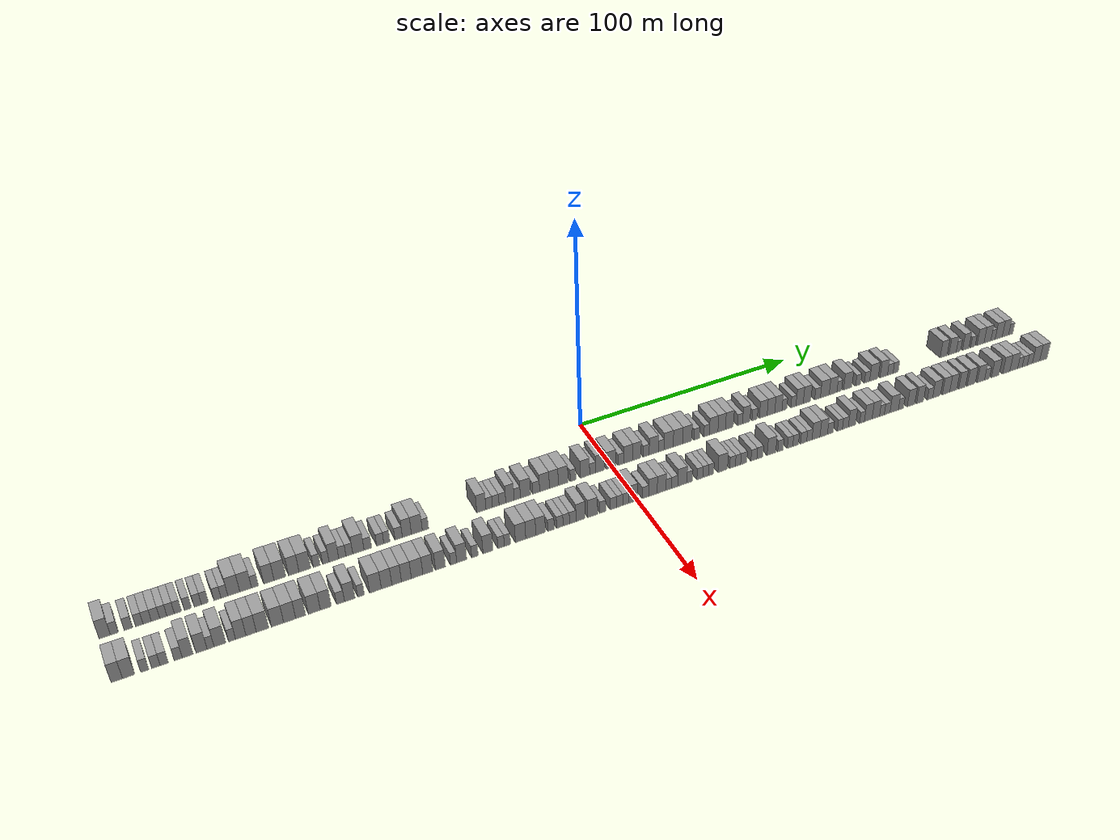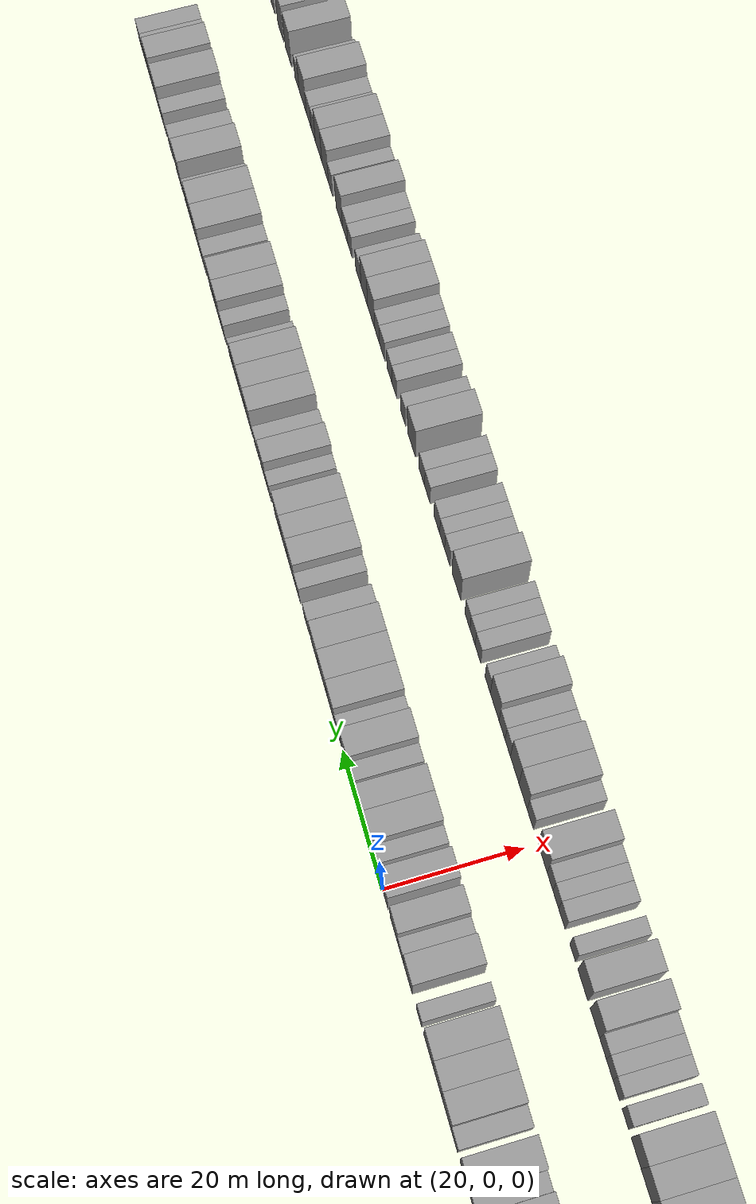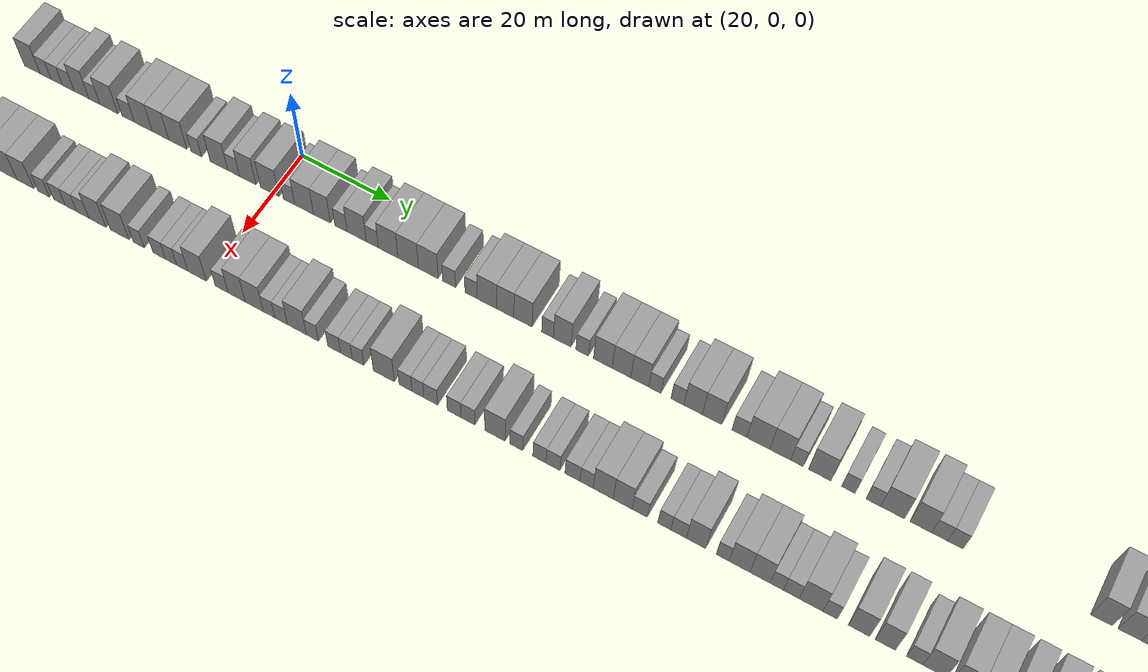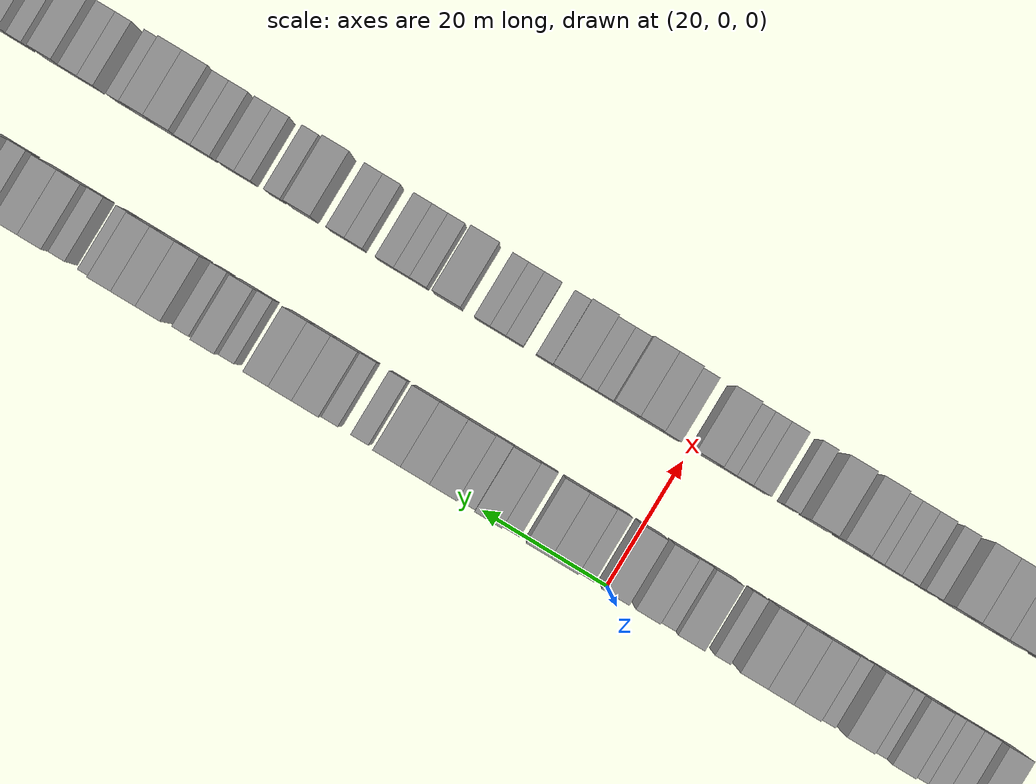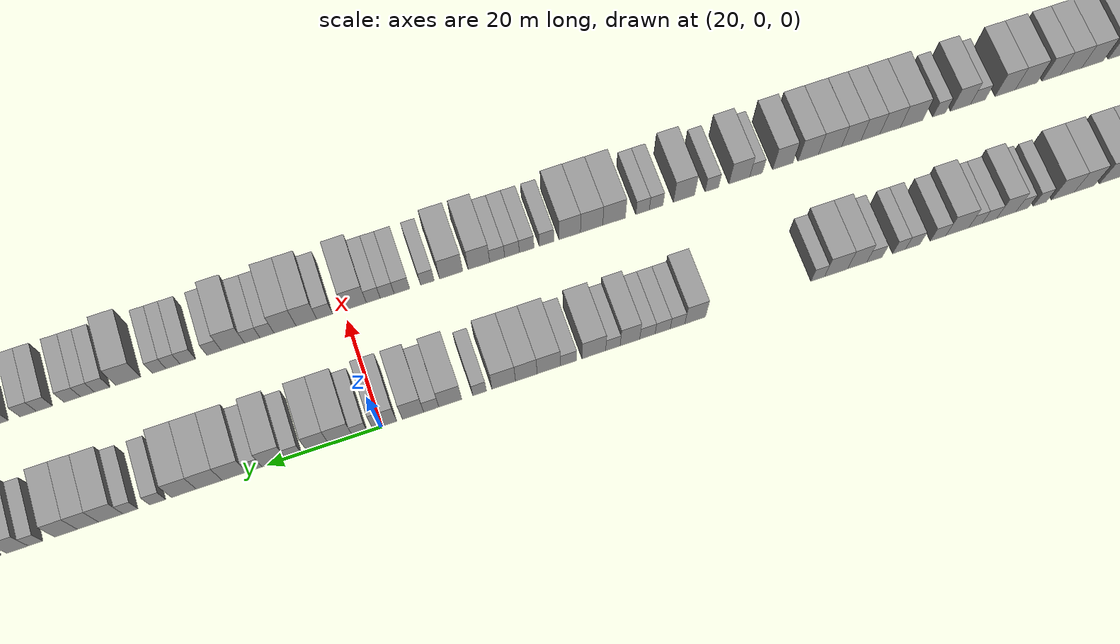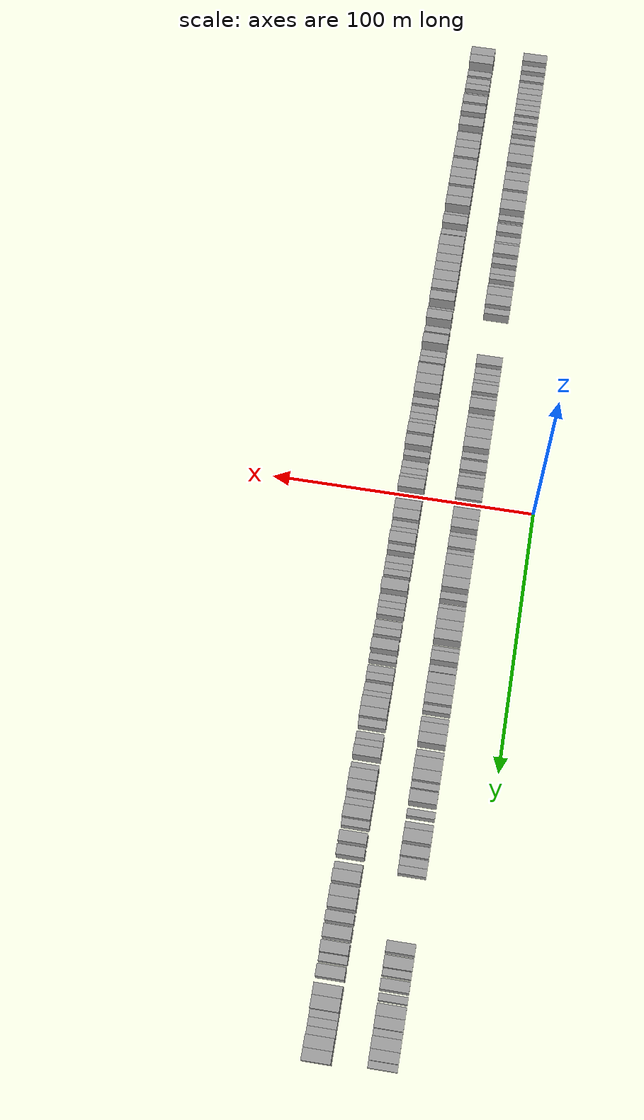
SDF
<sdf version="1.6">
 <world name="default">
  <scene>
   <sky><clouds><speed>12</speed></clouds></sky>
   <ambient>0.4 0.4 0.4 1</ambient>
   <background>0.7 0.7 0.7 1</background>
   <shadows>1</shadows>
  </scene>
  <gravity>0 0 -9.8066</gravity>
  <magnetic_field>6e-06 2.3e-05 -4.2e-05</magnetic_field>
  <physics default="0" name="default_physics" type="ode">
   <ode>
    <solver>
     <type>quick</type>
     <iters>10</iters>
     <sor>1.0</sor>
     <use_dynamic_moi_rescaling>0</use_dynamic_moi_rescaling>
    </solver>
    <constraints>
     <cfm>0</cfm>
     <erp>0.2</erp>
     <contact_max_correcting_vel>100</contact_max_correcting_vel>
     <contact_surface_layer>0.001</contact_surface_layer>
    </constraints>
   </ode>
   <max_step_size>0.004</max_step_size>
   <real_time_factor>1</real_time_factor>
   <real_time_update_rate>250</real_time_update_rate>
  </physics>
  <light name="sun" type="directional">
   <pose>0 0 10 0 0 0</pose>
   <diffuse>0.8 0.8 0.8 1</diffuse>
   <specular>0.2 0.2 0.2 1</specular>
   <attenuation>
    <range>1000</range>
    <constant>0.9</constant>
    <linear>0.01</linear>
    <quadratic>0.001</quadratic>
   </attenuation>
   <direction>-0.5 0.1 -0.9</direction>
  </light>
  <model name="building_1">
   <static>1</static>
   <pose>25.0000 -200.0431 0 0.000000 0.000000 0.000000</pose>
   <link name="link">
    <pose>0 0 4.50 0 0 0</pose>
    <collision name="collision"><geometry><box><size>10.0000 3.9137 9.0000</size></box></geometry></collision>
    <visual name="visual">
     <cast_shadows>0</cast_shadows>
     <geometry><box><size>10.0000 3.9137 9.0000</size></box></geometry>
     <material>
      <script>
       <uri>model://grey_wall/materials/scripts</uri>
       <uri>model://grey_wall/materials/textures</uri>
       <name>vrc/grey_wall</name>
      </script>
     </material>
    </visual>
   </link>
  </model>
  <model name="building_2">
   <static>1</static>
   <pose>25.0000 -196.7073 0 0.000000 0.000000 0.000000</pose>
   <link name="link">
    <pose>0 0 3.00 0 0 0</pose>
    <collision name="collision"><geometry><box><size>10.0000 2.7580 6.0000</size></box></geometry></collision>
    <visual name="visual">
     <cast_shadows>0</cast_shadows>
     <geometry><box><size>10.0000 2.7580 6.0000</size></box></geometry>
     <material>
      <script>
       <uri>model://grey_wall/materials/scripts</uri>
       <uri>model://grey_wall/materials/textures</uri>
       <name>vrc/grey_wall</name>
      </script>
     </material>
    </visual>
   </link>
  </model>
  <model name="building_3">
   <static>1</static>
   <pose>25.0000 -191.8505 0 0.000000 0.000000 0.000000</pose>
   <link name="link">
    <pose>0 0 3.00 0 0 0</pose>
    <collision name="collision"><geometry><box><size>10.0000 2.9555 6.0000</size></box></geometry></collision>
    <visual name="visual">
     <cast_shadows>0</cast_shadows>
     <geometry><box><size>10.0000 2.9555 6.0000</size></box></geometry>
     <material>
      <script>
       <uri>model://grey_wall/materials/scripts</uri>
       <uri>model://grey_wall/materials/textures</uri>
       <name>vrc/grey_wall</name>
      </script>
     </material>
    </visual>
   </link>
  </model>
  <model name="building_4">
   <static>1</static>
   <pose>25.0000 -188.0546 0 0.000000 0.000000 0.000000</pose>
   <link name="link">
    <pose>0 0 3.00 0 0 0</pose>
    <collision name="collision"><geometry><box><size>10.0000 2.6365 6.0000</size></box></geometry></collision>
    <visual name="visual">
     <cast_shadows>0</cast_shadows>
     <geometry><box><size>10.0000 2.6365 6.0000</size></box></geometry>
     <material>
      <script>
       <uri>model://grey_wall/materials/scripts</uri>
       <uri>model://grey_wall/materials/textures</uri>
       <name>vrc/grey_wall</name>
      </script>
     </material>
    </visual>
   </link>
  </model>
  <model name="building_5">
   <static>1</static>
   <pose>25.0000 -185.2900 0 0.000000 0.000000 0.000000</pose>
   <link name="link">
    <pose>0 0 3.00 0 0 0</pose>
    <collision name="collision"><geometry><box><size>10.0000 2.8927 6.0000</size></box></geometry></collision>
    <visual name="visual">
     <cast_shadows>0</cast_shadows>
     <geometry><box><size>10.0000 2.8927 6.0000</size></box></geometry>
     <material>
      <script>
       <uri>model://grey_wall/materials/scripts</uri>
       <uri>model://grey_wall/materials/textures</uri>
       <name>vrc/grey_wall</name>
      </script>
     </material>
    </visual>
   </link>
  </model>
  <model name="building_6">
   <static>1</static>
   <pose>25.0000 -182.3802 0 0.000000 0.000000 0.000000</pose>
   <link name="link">
    <pose>0 0 3.00 0 0 0</pose>
    <collision name="collision"><geometry><box><size>10.0000 2.9268 6.0000</size></box></geometry></collision>
    <visual name="visual">
     <cast_shadows>0</cast_shadows>
     <geometry><box><size>10.0000 2.9268 6.0000</size></box></geometry>
     <material>
      <script>
       <uri>model://grey_wall/materials/scripts</uri>
       <uri>model://grey_wall/materials/textures</uri>
       <name>vrc/grey_wall</name>
      </script>
     </material>
    </visual>
   </link>
  </model>
  <model name="building_7">
   <static>1</static>
   <pose>25.0000 -179.6508 0 0.000000 0.000000 0.000000</pose>
   <link name="link">
    <pose>0 0 3.00 0 0 0</pose>
    <collision name="collision"><geometry><box><size>10.0000 2.5320 6.0000</size></box></geometry></collision>
    <visual name="visual">
     <cast_shadows>0</cast_shadows>
     <geometry><box><size>10.0000 2.5320 6.0000</size></box></geometry>
     <material>
      <script>
       <uri>model://grey_wall/materials/scripts</uri>
       <uri>model://grey_wall/materials/textures</uri>
       <name>vrc/grey_wall</name>
      </script>
     </material>
    </visual>
   </link>
  </model>
  <model name="building_8">
   <static>1</static>
   <pose>25.0000 -177.0673 0 0.000000 0.000000 0.000000</pose>
   <link name="link">
    <pose>0 0 3.00 0 0 0</pose>
    <collision name="collision"><geometry><box><size>10.0000 2.6349 6.0000</size></box></geometry></collision>
    <visual name="visual">
     <cast_shadows>0</cast_shadows>
     <geometry><box><size>10.0000 2.6349 6.0000</size></box></geometry>
     <material>
      <script>
       <uri>model://grey_wall/materials/scripts</uri>
       <uri>model://grey_wall/materials/textures</uri>
       <name>vrc/grey_wall</name>
      </script>
     </material>
    </visual>
   </link>
  </model>
  <model name="building_9">
   <static>1</static>
   <pose>25.0000 -174.4618 0 0.000000 0.000000 0.000000</pose>
   <link name="link">
    <pose>0 0 3.00 0 0 0</pose>
    <collision name="collision"><geometry><box><size>10.0000 2.5761 6.0000</size></box></geometry></collision>
    <visual name="visual">
     <cast_shadows>0</cast_shadows>
     <geometry><box><size>10.0000 2.5761 6.0000</size></box></geometry>
     <material>
      <script>
       <uri>model://grey_wall/materials/scripts</uri>
       <uri>model://grey_wall/materials/textures</uri>
       <name>vrc/grey_wall</name>
      </script>
     </material>
    </visual>
   </link>
  </model>
  <model name="building_10">
   <static>1</static>
   <pose>25.0000 -170.8962 0 0.000000 0.000000 0.000000</pose>
   <link name="link">
    <pose>0 0 3.00 0 0 0</pose>
    <collision name="collision"><geometry><box><size>10.0000 2.5550 6.0000</size></box></geometry></collision>
    <visual name="visual">
     <cast_shadows>0</cast_shadows>
     <geometry><box><size>10.0000 2.5550 6.0000</size></box></geometry>
     <material>
      <script>
       <uri>model://grey_wall/materials/scripts</uri>
       <uri>model://grey_wall/materials/textures</uri>
       <name>vrc/grey_wall</name>
      </script>
     </material>
    </visual>
   </link>
  </model>
  <model name="building_11">
   <static>1</static>
   <pose>25.0000 -167.3284 0 0.000000 0.000000 0.000000</pose>
   <link name="link">
    <pose>0 0 3.00 0 0 0</pose>
    <collision name="collision"><geometry><box><size>10.0000 2.5806 6.0000</size></box></geometry></collision>
    <visual name="visual">
     <cast_shadows>0</cast_shadows>
     <geometry><box><size>10.0000 2.5806 6.0000</size></box></geometry>
     <material>
      <script>
       <uri>model://grey_wall/materials/scripts</uri>
       <uri>model://grey_wall/materials/textures</uri>
       <name>vrc/grey_wall</name>
      </script>
     </material>
    </visual>
   </link>
  </model>
  <model name="building_12">
   <static>1</static>
   <pose>25.0000 -164.7689 0 0.000000 0.000000 0.000000</pose>
   <link name="link">
    <pose>0 0 3.00 0 0 0</pose>
    <collision name="collision"><geometry><box><size>10.0000 2.5385 6.0000</size></box></geometry></collision>
    <visual name="visual">
     <cast_shadows>0</cast_shadows>
     <geometry><box><size>10.0000 2.5385 6.0000</size></box></geometry>
     <material>
      <script>
       <uri>model://grey_wall/materials/scripts</uri>
       <uri>model://grey_wall/materials/textures</uri>
       <name>vrc/grey_wall</name>
      </script>
     </material>
    </visual>
   </link>
  </model>
  <model name="building_13">
   <static>1</static>
   <pose>25.0000 -160.2340 0 0.000000 0.000000 0.000000</pose>
   <link name="link">
    <pose>0 0 3.00 0 0 0</pose>
    <collision name="collision"><geometry><box><size>10.0000 2.5311 6.0000</size></box></geometry></collision>
    <visual name="visual">
     <cast_shadows>0</cast_shadows>
     <geometry><box><size>10.0000 2.5311 6.0000</size></box></geometry>
     <material>
      <script>
       <uri>model://grey_wall/materials/scripts</uri>
       <uri>model://grey_wall/materials/textures</uri>
       <name>vrc/grey_wall</name>
      </script>
     </material>
    </visual>
   </link>
  </model>
  <model name="building_14">
   <static>1</static>
   <pose>25.0000 -157.7201 0 0.000000 0.000000 0.000000</pose>
   <link name="link">
    <pose>0 0 3.00 0 0 0</pose>
    <collision name="collision"><geometry><box><size>10.0000 2.4967 6.0000</size></box></geometry></collision>
    <visual name="visual">
     <cast_shadows>0</cast_shadows>
     <geometry><box><size>10.0000 2.4967 6.0000</size></box></geometry>
     <material>
      <script>
       <uri>model://grey_wall/materials/scripts</uri>
       <uri>model://grey_wall/materials/textures</uri>
       <name>vrc/grey_wall</name>
      </script>
     </material>
    </visual>
   </link>
  </model>
  <model name="building_15">
   <static>1</static>
   <pose>25.0000 -154.2740 0 0.000000 0.000000 0.000000</pose>
   <link name="link">
    <pose>0 0 4.50 0 0 0</pose>
    <collision name="collision"><geometry><box><size>10.0000 4.3956 9.0000</size></box></geometry></collision>
    <visual name="visual">
     <cast_shadows>0</cast_shadows>
     <geometry><box><size>10.0000 4.3956 9.0000</size></box></geometry>
     <material>
      <script>
       <uri>model://grey_wall/materials/scripts</uri>
       <uri>model://grey_wall/materials/textures</uri>
       <name>vrc/grey_wall</name>
      </script>
     </material>
    </visual>
   </link>
  </model>
  <model name="building_16">
   <static>1</static>
   <pose>25.0000 -149.9144 0 0.000000 0.000000 0.000000</pose>
   <link name="link">
    <pose>0 0 4.50 0 0 0</pose>
    <collision name="collision"><geometry><box><size>10.0000 4.3236 9.0000</size></box></geometry></collision>
    <visual name="visual">
     <cast_shadows>0</cast_shadows>
     <geometry><box><size>10.0000 4.3236 9.0000</size></box></geometry>
     <material>
      <script>
       <uri>model://grey_wall/materials/scripts</uri>
       <uri>model://grey_wall/materials/textures</uri>
       <name>vrc/grey_wall</name>
      </script>
     </material>
    </visual>
   </link>
  </model>
  <model name="building_17">
   <static>1</static>
   <pose>25.0000 -146.4588 0 0.000000 0.000000 0.000000</pose>
   <link name="link">
    <pose>0 0 3.00 0 0 0</pose>
    <collision name="collision"><geometry><box><size>10.0000 2.5877 6.0000</size></box></geometry></collision>
    <visual name="visual">
     <cast_shadows>0</cast_shadows>
     <geometry><box><size>10.0000 2.5877 6.0000</size></box></geometry>
     <material>
      <script>
       <uri>model://grey_wall/materials/scripts</uri>
       <uri>model://grey_wall/materials/textures</uri>
       <name>vrc/grey_wall</name>
      </script>
     </material>
    </visual>
   </link>
  </model>
  <model name="building_18">
   <static>1</static>
   <pose>25.0000 -141.2487 0 0.000000 0.000000 0.000000</pose>
   <link name="link">
    <pose>0 0 4.50 0 0 0</pose>
    <collision name="collision"><geometry><box><size>10.0000 3.8325 9.0000</size></box></geometry></collision>
    <visual name="visual">
     <cast_shadows>0</cast_shadows>
     <geometry><box><size>10.0000 3.8325 9.0000</size></box></geometry>
     <material>
      <script>
       <uri>model://grey_wall/materials/scripts</uri>
       <uri>model://grey_wall/materials/textures</uri>
       <name>vrc/grey_wall</name>
      </script>
     </material>
    </visual>
   </link>
  </model>
  <model name="building_19">
   <static>1</static>
   <pose>25.0000 -137.1106 0 0.000000 0.000000 0.000000</pose>
   <link name="link">
    <pose>0 0 4.50 0 0 0</pose>
    <collision name="collision"><geometry><box><size>10.0000 4.4438 9.0000</size></box></geometry></collision>
    <visual name="visual">
     <cast_shadows>0</cast_shadows>
     <geometry><box><size>10.0000 4.4438 9.0000</size></box></geometry>
     <material>
      <script>
       <uri>model://grey_wall/materials/scripts</uri>
       <uri>model://grey_wall/materials/textures</uri>
       <name>vrc/grey_wall</name>
      </script>
     </material>
    </visual>
   </link>
  </model>
  <model name="building_20">
   <static>1</static>
   <pose>25.0000 -131.8946 0 0.000000 0.000000 0.000000</pose>
   <link name="link">
    <pose>0 0 4.50 0 0 0</pose>
    <collision name="collision"><geometry><box><size>10.0000 3.9882 9.0000</size></box></geometry></collision>
    <visual name="visual">
     <cast_shadows>0</cast_shadows>
     <geometry><box><size>10.0000 3.9882 9.0000</size></box></geometry>
     <material>
      <script>
       <uri>model://grey_wall/materials/scripts</uri>
       <uri>model://grey_wall/materials/textures</uri>
       <name>vrc/grey_wall</name>
      </script>
     </material>
    </visual>
   </link>
  </model>
  <model name="building_21">
   <static>1</static>
   <pose>25.0000 -127.6713 0 0.000000 0.000000 0.000000</pose>
   <link name="link">
    <pose>0 0 4.50 0 0 0</pose>
    <collision name="collision"><geometry><box><size>10.0000 4.4585 9.0000</size></box></geometry></collision>
    <visual name="visual">
     <cast_shadows>0</cast_shadows>
     <geometry><box><size>10.0000 4.4585 9.0000</size></box></geometry>
     <material>
      <script>
       <uri>model://grey_wall/materials/scripts</uri>
       <uri>model://grey_wall/materials/textures</uri>
       <name>vrc/grey_wall</name>
      </script>
     </material>
    </visual>
   </link>
  </model>
  <model name="building_22">
   <static>1</static>
   <pose>25.0000 -123.1345 0 0.000000 0.000000 0.000000</pose>
   <link name="link">
    <pose>0 0 3.00 0 0 0</pose>
    <collision name="collision"><geometry><box><size>10.0000 2.6150 6.0000</size></box></geometry></collision>
    <visual name="visual">
     <cast_shadows>0</cast_shadows>
     <geometry><box><size>10.0000 2.6150 6.0000</size></box></geometry>
     <material>
      <script>
       <uri>model://grey_wall/materials/scripts</uri>
       <uri>model://grey_wall/materials/textures</uri>
       <name>vrc/grey_wall</name>
      </script>
     </material>
    </visual>
   </link>
  </model>
  <model name="building_23">
   <static>1</static>
   <pose>25.0000 -119.6156 0 0.000000 0.000000 0.000000</pose>
   <link name="link">
    <pose>0 0 3.00 0 0 0</pose>
    <collision name="collision"><geometry><box><size>10.0000 2.4228 6.0000</size></box></geometry></collision>
    <visual name="visual">
     <cast_shadows>0</cast_shadows>
     <geometry><box><size>10.0000 2.4228 6.0000</size></box></geometry>
     <material>
      <script>
       <uri>model://grey_wall/materials/scripts</uri>
       <uri>model://grey_wall/materials/textures</uri>
       <name>vrc/grey_wall</name>
      </script>
     </material>
    </visual>
   </link>
  </model>
  <model name="building_24">
   <static>1</static>
   <pose>25.0000 -116.5192 0 0.000000 0.000000 0.000000</pose>
   <link name="link">
    <pose>0 0 4.50 0 0 0</pose>
    <collision name="collision"><geometry><box><size>10.0000 3.7701 9.0000</size></box></geometry></collision>
    <visual name="visual">
     <cast_shadows>0</cast_shadows>
     <geometry><box><size>10.0000 3.7701 9.0000</size></box></geometry>
     <material>
      <script>
       <uri>model://grey_wall/materials/scripts</uri>
       <uri>model://grey_wall/materials/textures</uri>
       <name>vrc/grey_wall</name>
      </script>
     </material>
    </visual>
   </link>
  </model>
  <model name="building_25">
   <static>1</static>
   <pose>25.0000 -113.2266 0 0.000000 0.000000 0.000000</pose>
   <link name="link">
    <pose>0 0 3.00 0 0 0</pose>
    <collision name="collision"><geometry><box><size>10.0000 2.8150 6.0000</size></box></geometry></collision>
    <visual name="visual">
     <cast_shadows>0</cast_shadows>
     <geometry><box><size>10.0000 2.8150 6.0000</size></box></geometry>
     <material>
      <script>
       <uri>model://grey_wall/materials/scripts</uri>
       <uri>model://grey_wall/materials/textures</uri>
       <name>vrc/grey_wall</name>
      </script>
     </material>
    </visual>
   </link>
  </model>
  <model name="building_26">
   <static>1</static>
   <pose>25.0000 -110.4952 0 0.000000 0.000000 0.000000</pose>
   <link name="link">
    <pose>0 0 3.00 0 0 0</pose>
    <collision name="collision"><geometry><box><size>10.0000 2.6478 6.0000</size></box></geometry></collision>
    <visual name="visual">
     <cast_shadows>0</cast_shadows>
     <geometry><box><size>10.0000 2.6478 6.0000</size></box></geometry>
     <material>
      <script>
       <uri>model://grey_wall/materials/scripts</uri>
       <uri>model://grey_wall/materials/textures</uri>
       <name>vrc/grey_wall</name>
      </script>
     </material>
    </visual>
   </link>
  </model>
  <model name="building_27">
   <static>1</static>
   <pose>25.0000 -106.9631 0 0.000000 0.000000 0.000000</pose>
   <link name="link">
    <pose>0 0 4.50 0 0 0</pose>
    <collision name="collision"><geometry><box><size>10.0000 4.4164 9.0000</size></box></geometry></collision>
    <visual name="visual">
     <cast_shadows>0</cast_shadows>
     <geometry><box><size>10.0000 4.4164 9.0000</size></box></geometry>
     <material>
      <script>
       <uri>model://grey_wall/materials/scripts</uri>
       <uri>model://grey_wall/materials/textures</uri>
       <name>vrc/grey_wall</name>
      </script>
     </material>
    </visual>
   </link>
  </model>
  <model name="building_28">
   <static>1</static>
   <pose>25.0000 -103.2580 0 0.000000 0.000000 0.000000</pose>
   <link name="link">
    <pose>0 0 3.00 0 0 0</pose>
    <collision name="collision"><geometry><box><size>10.0000 2.9938 6.0000</size></box></geometry></collision>
    <visual name="visual">
     <cast_shadows>0</cast_shadows>
     <geometry><box><size>10.0000 2.9938 6.0000</size></box></geometry>
     <material>
      <script>
       <uri>model://grey_wall/materials/scripts</uri>
       <uri>model://grey_wall/materials/textures</uri>
       <name>vrc/grey_wall</name>
      </script>
     </material>
    </visual>
   </link>
  </model>
  <model name="building_29">
   <static>1</static>
   <pose>25.0000 -98.3528 0 0.000000 0.000000 0.000000</pose>
   <link name="link">
    <pose>0 0 3.00 0 0 0</pose>
    <collision name="collision"><geometry><box><size>10.0000 2.8166 6.0000</size></box></geometry></collision>
    <visual name="visual">
     <cast_shadows>0</cast_shadows>
     <geometry><box><size>10.0000 2.8166 6.0000</size></box></geometry>
     <material>
      <script>
       <uri>model://grey_wall/materials/scripts</uri>
       <uri>model://grey_wall/materials/textures</uri>
       <name>vrc/grey_wall</name>
      </script>
     </material>
    </visual>
   </link>
  </model>
  <model name="building_30">
   <static>1</static>
   <pose>25.0000 -95.7208 0 0.000000 0.000000 0.000000</pose>
   <link name="link">
    <pose>0 0 3.00 0 0 0</pose>
    <collision name="collision"><geometry><box><size>10.0000 2.4473 6.0000</size></box></geometry></collision>
    <visual name="visual">
     <cast_shadows>0</cast_shadows>
     <geometry><box><size>10.0000 2.4473 6.0000</size></box></geometry>
     <material>
      <script>
       <uri>model://grey_wall/materials/scripts</uri>
       <uri>model://grey_wall/materials/textures</uri>
       <name>vrc/grey_wall</name>
      </script>
     </material>
    </visual>
   </link>
  </model>
  <model name="building_31">
   <static>1</static>
   <pose>25.0000 -91.0076 0 0.000000 0.000000 0.000000</pose>
   <link name="link">
    <pose>0 0 3.00 0 0 0</pose>
    <collision name="collision"><geometry><box><size>10.0000 2.9791 6.0000</size></box></geometry></collision>
    <visual name="visual">
     <cast_shadows>0</cast_shadows>
     <geometry><box><size>10.0000 2.9791 6.0000</size></box></geometry>
     <material>
      <script>
       <uri>model://grey_wall/materials/scripts</uri>
       <uri>model://grey_wall/materials/textures</uri>
       <name>vrc/grey_wall</name>
      </script>
     </material>
    </visual>
   </link>
  </model>
  <model name="building_32">
   <static>1</static>
   <pose>25.0000 -87.6984 0 0.000000 0.000000 0.000000</pose>
   <link name="link">
    <pose>0 0 4.50 0 0 0</pose>
    <collision name="collision"><geometry><box><size>10.0000 3.6393 9.0000</size></box></geometry></collision>
    <visual name="visual">
     <cast_shadows>0</cast_shadows>
     <geometry><box><size>10.0000 3.6393 9.0000</size></box></geometry>
     <material>
      <script>
       <uri>model://grey_wall/materials/scripts</uri>
       <uri>model://grey_wall/materials/textures</uri>
       <name>vrc/grey_wall</name>
      </script>
     </material>
    </visual>
   </link>
  </model>
  <model name="building_33">
   <static>1</static>
   <pose>25.0000 -83.6790 0 0.000000 0.000000 0.000000</pose>
   <link name="link">
    <pose>0 0 4.50 0 0 0</pose>
    <collision name="collision"><geometry><box><size>10.0000 4.3994 9.0000</size></box></geometry></collision>
    <visual name="visual">
     <cast_shadows>0</cast_shadows>
     <geometry><box><size>10.0000 4.3994 9.0000</size></box></geometry>
     <material>
      <script>
       <uri>model://grey_wall/materials/scripts</uri>
       <uri>model://grey_wall/materials/textures</uri>
       <name>vrc/grey_wall</name>
      </script>
     </material>
    </visual>
   </link>
  </model>
  <model name="building_34">
   <static>1</static>
   <pose>25.0000 -80.1914 0 0.000000 0.000000 0.000000</pose>
   <link name="link">
    <pose>0 0 3.00 0 0 0</pose>
    <collision name="collision"><geometry><box><size>10.0000 2.5758 6.0000</size></box></geometry></collision>
    <visual name="visual">
     <cast_shadows>0</cast_shadows>
     <geometry><box><size>10.0000 2.5758 6.0000</size></box></geometry>
     <material>
      <script>
       <uri>model://grey_wall/materials/scripts</uri>
       <uri>model://grey_wall/materials/textures</uri>
       <name>vrc/grey_wall</name>
      </script>
     </material>
    </visual>
   </link>
  </model>
  <model name="building_35">
   <static>1</static>
   <pose>25.0000 -57.1080 0 0.000000 0.000000 0.000000</pose>
   <link name="link">
    <pose>0 0 4.50 0 0 0</pose>
    <collision name="collision"><geometry><box><size>10.0000 3.8637 9.0000</size></box></geometry></collision>
    <visual name="visual">
     <cast_shadows>0</cast_shadows>
     <geometry><box><size>10.0000 3.8637 9.0000</size></box></geometry>
     <material>
      <script>
       <uri>model://grey_wall/materials/scripts</uri>
       <uri>model://grey_wall/materials/textures</uri>
       <name>vrc/grey_wall</name>
      </script>
     </material>
    </visual>
   </link>
  </model>
  <model name="building_36">
   <static>1</static>
   <pose>25.0000 -53.8150 0 0.000000 0.000000 0.000000</pose>
   <link name="link">
    <pose>0 0 3.00 0 0 0</pose>
    <collision name="collision"><geometry><box><size>10.0000 2.7222 6.0000</size></box></geometry></collision>
    <visual name="visual">
     <cast_shadows>0</cast_shadows>
     <geometry><box><size>10.0000 2.7222 6.0000</size></box></geometry>
     <material>
      <script>
       <uri>model://grey_wall/materials/scripts</uri>
       <uri>model://grey_wall/materials/textures</uri>
       <name>vrc/grey_wall</name>
      </script>
     </material>
    </visual>
   </link>
  </model>
  <model name="building_37">
   <static>1</static>
   <pose>25.0000 -51.0576 0 0.000000 0.000000 0.000000</pose>
   <link name="link">
    <pose>0 0 3.00 0 0 0</pose>
    <collision name="collision"><geometry><box><size>10.0000 2.7926 6.0000</size></box></geometry></collision>
    <visual name="visual">
     <cast_shadows>0</cast_shadows>
     <geometry><box><size>10.0000 2.7926 6.0000</size></box></geometry>
     <material>
      <script>
       <uri>model://grey_wall/materials/scripts</uri>
       <uri>model://grey_wall/materials/textures</uri>
       <name>vrc/grey_wall</name>
      </script>
     </material>
    </visual>
   </link>
  </model>
  <model name="building_38">
   <static>1</static>
   <pose>25.0000 -48.2400 0 0.000000 0.000000 0.000000</pose>
   <link name="link">
    <pose>0 0 3.00 0 0 0</pose>
    <collision name="collision"><geometry><box><size>10.0000 2.8425 6.0000</size></box></geometry></collision>
    <visual name="visual">
     <cast_shadows>0</cast_shadows>
     <geometry><box><size>10.0000 2.8425 6.0000</size></box></geometry>
     <material>
      <script>
       <uri>model://grey_wall/materials/scripts</uri>
       <uri>model://grey_wall/materials/textures</uri>
       <name>vrc/grey_wall</name>
      </script>
     </material>
    </visual>
   </link>
  </model>
  <model name="building_39">
   <static>1</static>
   <pose>25.0000 -45.0187 0 0.000000 0.000000 0.000000</pose>
   <link name="link">
    <pose>0 0 4.50 0 0 0</pose>
    <collision name="collision"><geometry><box><size>10.0000 3.6001 9.0000</size></box></geometry></collision>
    <visual name="visual">
     <cast_shadows>0</cast_shadows>
     <geometry><box><size>10.0000 3.6001 9.0000</size></box></geometry>
     <material>
      <script>
       <uri>model://grey_wall/materials/scripts</uri>
       <uri>model://grey_wall/materials/textures</uri>
       <name>vrc/grey_wall</name>
      </script>
     </material>
    </visual>
   </link>
  </model>
  <model name="building_40">
   <static>1</static>
   <pose>25.0000 -41.8844 0 0.000000 0.000000 0.000000</pose>
   <link name="link">
    <pose>0 0 3.00 0 0 0</pose>
    <collision name="collision"><geometry><box><size>10.0000 2.6685 6.0000</size></box></geometry></collision>
    <visual name="visual">
     <cast_shadows>0</cast_shadows>
     <geometry><box><size>10.0000 2.6685 6.0000</size></box></geometry>
     <material>
      <script>
       <uri>model://grey_wall/materials/scripts</uri>
       <uri>model://grey_wall/materials/textures</uri>
       <name>vrc/grey_wall</name>
      </script>
     </material>
    </visual>
   </link>
  </model>
  <model name="building_41">
   <static>1</static>
   <pose>25.0000 -38.3859 0 0.000000 0.000000 0.000000</pose>
   <link name="link">
    <pose>0 0 4.50 0 0 0</pose>
    <collision name="collision"><geometry><box><size>10.0000 4.3285 9.0000</size></box></geometry></collision>
    <visual name="visual">
     <cast_shadows>0</cast_shadows>
     <geometry><box><size>10.0000 4.3285 9.0000</size></box></geometry>
     <material>
      <script>
       <uri>model://grey_wall/materials/scripts</uri>
       <uri>model://grey_wall/materials/textures</uri>
       <name>vrc/grey_wall</name>
      </script>
     </material>
    </visual>
   </link>
  </model>
  <model name="building_42">
   <static>1</static>
   <pose>25.0000 -33.7441 0 0.000000 0.000000 0.000000</pose>
   <link name="link">
    <pose>0 0 3.00 0 0 0</pose>
    <collision name="collision"><geometry><box><size>10.0000 2.9551 6.0000</size></box></geometry></collision>
    <visual name="visual">
     <cast_shadows>0</cast_shadows>
     <geometry><box><size>10.0000 2.9551 6.0000</size></box></geometry>
     <material>
      <script>
       <uri>model://grey_wall/materials/scripts</uri>
       <uri>model://grey_wall/materials/textures</uri>
       <name>vrc/grey_wall</name>
      </script>
     </material>
    </visual>
   </link>
  </model>
  <model name="building_43">
   <static>1</static>
   <pose>25.0000 -30.1479 0 0.000000 0.000000 0.000000</pose>
   <link name="link">
    <pose>0 0 4.50 0 0 0</pose>
    <collision name="collision"><geometry><box><size>10.0000 4.2372 9.0000</size></box></geometry></collision>
    <visual name="visual">
     <cast_shadows>0</cast_shadows>
     <geometry><box><size>10.0000 4.2372 9.0000</size></box></geometry>
     <material>
      <script>
       <uri>model://grey_wall/materials/scripts</uri>
       <uri>model://grey_wall/materials/textures</uri>
       <name>vrc/grey_wall</name>
      </script>
     </material>
    </visual>
   </link>
  </model>
  <model name="building_44">
   <static>1</static>
   <pose>25.0000 -26.0718 0 0.000000 0.000000 0.000000</pose>
   <link name="link">
    <pose>0 0 4.50 0 0 0</pose>
    <collision name="collision"><geometry><box><size>10.0000 3.9150 9.0000</size></box></geometry></collision>
    <visual name="visual">
     <cast_shadows>0</cast_shadows>
     <geometry><box><size>10.0000 3.9150 9.0000</size></box></geometry>
     <material>
      <script>
       <uri>model://grey_wall/materials/scripts</uri>
       <uri>model://grey_wall/materials/textures</uri>
       <name>vrc/grey_wall</name>
      </script>
     </material>
    </visual>
   </link>
  </model>
  <model name="building_45">
   <static>1</static>
   <pose>25.0000 -21.9916 0 0.000000 0.000000 0.000000</pose>
   <link name="link">
    <pose>0 0 4.50 0 0 0</pose>
    <collision name="collision"><geometry><box><size>10.0000 4.2454 9.0000</size></box></geometry></collision>
    <visual name="visual">
     <cast_shadows>0</cast_shadows>
     <geometry><box><size>10.0000 4.2454 9.0000</size></box></geometry>
     <material>
      <script>
       <uri>model://grey_wall/materials/scripts</uri>
       <uri>model://grey_wall/materials/textures</uri>
       <name>vrc/grey_wall</name>
      </script>
     </material>
    </visual>
   </link>
  </model>
  <model name="building_46">
   <static>1</static>
   <pose>25.0000 -17.6397 0 0.000000 0.000000 0.000000</pose>
   <link name="link">
    <pose>0 0 3.00 0 0 0</pose>
    <collision name="collision"><geometry><box><size>10.0000 2.4583 6.0000</size></box></geometry></collision>
    <visual name="visual">
     <cast_shadows>0</cast_shadows>
     <geometry><box><size>10.0000 2.4583 6.0000</size></box></geometry>
     <material>
      <script>
       <uri>model://grey_wall/materials/scripts</uri>
       <uri>model://grey_wall/materials/textures</uri>
       <name>vrc/grey_wall</name>
      </script>
     </material>
    </visual>
   </link>
  </model>
  <model name="building_47">
   <static>1</static>
   <pose>25.0000 -12.3555 0 0.000000 0.000000 0.000000</pose>
   <link name="link">
    <pose>0 0 4.50 0 0 0</pose>
    <collision name="collision"><geometry><box><size>10.0000 4.1102 9.0000</size></box></geometry></collision>
    <visual name="visual">
     <cast_shadows>0</cast_shadows>
     <geometry><box><size>10.0000 4.1102 9.0000</size></box></geometry>
     <material>
      <script>
       <uri>model://grey_wall/materials/scripts</uri>
       <uri>model://grey_wall/materials/textures</uri>
       <name>vrc/grey_wall</name>
      </script>
     </material>
    </visual>
   </link>
  </model>
  <model name="building_48">
   <static>1</static>
   <pose>25.0000 -8.9529 0 0.000000 0.000000 0.000000</pose>
   <link name="link">
    <pose>0 0 3.00 0 0 0</pose>
    <collision name="collision"><geometry><box><size>10.0000 2.6950 6.0000</size></box></geometry></collision>
    <visual name="visual">
     <cast_shadows>0</cast_shadows>
     <geometry><box><size>10.0000 2.6950 6.0000</size></box></geometry>
     <material>
      <script>
       <uri>model://grey_wall/materials/scripts</uri>
       <uri>model://grey_wall/materials/textures</uri>
       <name>vrc/grey_wall</name>
      </script>
     </material>
    </visual>
   </link>
  </model>
  <model name="building_49">
   <static>1</static>
   <pose>25.0000 -5.7064 0 0.000000 0.000000 0.000000</pose>
   <link name="link">
    <pose>0 0 4.50 0 0 0</pose>
    <collision name="collision"><geometry><box><size>10.0000 3.7981 9.0000</size></box></geometry></collision>
    <visual name="visual">
     <cast_shadows>0</cast_shadows>
     <geometry><box><size>10.0000 3.7981 9.0000</size></box></geometry>
     <material>
      <script>
       <uri>model://grey_wall/materials/scripts</uri>
       <uri>model://grey_wall/materials/textures</uri>
       <name>vrc/grey_wall</name>
      </script>
     </material>
    </visual>
   </link>
  </model>
  <model name="building_50">
   <static>1</static>
   <pose>25.0000 -0.6873 0 0.000000 0.000000 0.000000</pose>
   <link name="link">
    <pose>0 0 4.50 0 0 0</pose>
    <collision name="collision"><geometry><box><size>10.0000 4.2400 9.0000</size></box></geometry></collision>
    <visual name="visual">
     <cast_shadows>0</cast_shadows>
     <geometry><box><size>10.0000 4.2400 9.0000</size></box></geometry>
     <material>
      <script>
       <uri>model://grey_wall/materials/scripts</uri>
       <uri>model://grey_wall/materials/textures</uri>
       <name>vrc/grey_wall</name>
      </script>
     </material>
    </visual>
   </link>
  </model>
  <model name="building_51">
   <static>1</static>
   <pose>25.0000 3.7216 0 0.000000 0.000000 0.000000</pose>
   <link name="link">
    <pose>0 0 3.00 0 0 0</pose>
    <collision name="collision"><geometry><box><size>10.0000 2.5778 6.0000</size></box></geometry></collision>
    <visual name="visual">
     <cast_shadows>0</cast_shadows>
     <geometry><box><size>10.0000 2.5778 6.0000</size></box></geometry>
     <material>
      <script>
       <uri>model://grey_wall/materials/scripts</uri>
       <uri>model://grey_wall/materials/textures</uri>
       <name>vrc/grey_wall</name>
      </script>
     </material>
    </visual>
   </link>
  </model>
  <model name="building_52">
   <static>1</static>
   <pose>25.0000 7.1169 0 0.000000 0.000000 0.000000</pose>
   <link name="link">
    <pose>0 0 4.50 0 0 0</pose>
    <collision name="collision"><geometry><box><size>10.0000 4.2129 9.0000</size></box></geometry></collision>
    <visual name="visual">
     <cast_shadows>0</cast_shadows>
     <geometry><box><size>10.0000 4.2129 9.0000</size></box></geometry>
     <material>
      <script>
       <uri>model://grey_wall/materials/scripts</uri>
       <uri>model://grey_wall/materials/textures</uri>
       <name>vrc/grey_wall</name>
      </script>
     </material>
    </visual>
   </link>
  </model>
  <model name="building_53">
   <static>1</static>
   <pose>25.0000 11.1153 0 0.000000 0.000000 0.000000</pose>
   <link name="link">
    <pose>0 0 4.50 0 0 0</pose>
    <collision name="collision"><geometry><box><size>10.0000 3.7839 9.0000</size></box></geometry></collision>
    <visual name="visual">
     <cast_shadows>0</cast_shadows>
     <geometry><box><size>10.0000 3.7839 9.0000</size></box></geometry>
     <material>
      <script>
       <uri>model://grey_wall/materials/scripts</uri>
       <uri>model://grey_wall/materials/textures</uri>
       <name>vrc/grey_wall</name>
      </script>
     </material>
    </visual>
   </link>
  </model>
  <model name="building_54">
   <static>1</static>
   <pose>25.0000 15.3685 0 0.000000 0.000000 0.000000</pose>
   <link name="link">
    <pose>0 0 3.00 0 0 0</pose>
    <collision name="collision"><geometry><box><size>10.0000 2.7225 6.0000</size></box></geometry></collision>
    <visual name="visual">
     <cast_shadows>0</cast_shadows>
     <geometry><box><size>10.0000 2.7225 6.0000</size></box></geometry>
     <material>
      <script>
       <uri>model://grey_wall/materials/scripts</uri>
       <uri>model://grey_wall/materials/textures</uri>
       <name>vrc/grey_wall</name>
      </script>
     </material>
    </visual>
   </link>
  </model>
  <model name="building_55">
   <static>1</static>
   <pose>25.0000 18.8446 0 0.000000 0.000000 0.000000</pose>
   <link name="link">
    <pose>0 0 4.50 0 0 0</pose>
    <collision name="collision"><geometry><box><size>10.0000 4.2296 9.0000</size></box></geometry></collision>
    <visual name="visual">
     <cast_shadows>0</cast_shadows>
     <geometry><box><size>10.0000 4.2296 9.0000</size></box></geometry>
     <material>
      <script>
       <uri>model://grey_wall/materials/scripts</uri>
       <uri>model://grey_wall/materials/textures</uri>
       <name>vrc/grey_wall</name>
      </script>
     </material>
    </visual>
   </link>
  </model>
  <model name="building_56">
   <static>1</static>
   <pose>25.0000 22.3115 0 0.000000 0.000000 0.000000</pose>
   <link name="link">
    <pose>0 0 3.00 0 0 0</pose>
    <collision name="collision"><geometry><box><size>10.0000 2.7043 6.0000</size></box></geometry></collision>
    <visual name="visual">
     <cast_shadows>0</cast_shadows>
     <geometry><box><size>10.0000 2.7043 6.0000</size></box></geometry>
     <material>
      <script>
       <uri>model://grey_wall/materials/scripts</uri>
       <uri>model://grey_wall/materials/textures</uri>
       <name>vrc/grey_wall</name>
      </script>
     </material>
    </visual>
   </link>
  </model>
  <model name="building_57">
   <static>1</static>
   <pose>25.0000 25.7868 0 0.000000 0.000000 0.000000</pose>
   <link name="link">
    <pose>0 0 4.50 0 0 0</pose>
    <collision name="collision"><geometry><box><size>10.0000 4.2463 9.0000</size></box></geometry></collision>
    <visual name="visual">
     <cast_shadows>0</cast_shadows>
     <geometry><box><size>10.0000 4.2463 9.0000</size></box></geometry>
     <material>
      <script>
       <uri>model://grey_wall/materials/scripts</uri>
       <uri>model://grey_wall/materials/textures</uri>
       <name>vrc/grey_wall</name>
      </script>
     </material>
    </visual>
   </link>
  </model>
  <model name="building_58">
   <static>1</static>
   <pose>25.0000 30.1371 0 0.000000 0.000000 0.000000</pose>
   <link name="link">
    <pose>0 0 4.50 0 0 0</pose>
    <collision name="collision"><geometry><box><size>10.0000 4.4542 9.0000</size></box></geometry></collision>
    <visual name="visual">
     <cast_shadows>0</cast_shadows>
     <geometry><box><size>10.0000 4.4542 9.0000</size></box></geometry>
     <material>
      <script>
       <uri>model://grey_wall/materials/scripts</uri>
       <uri>model://grey_wall/materials/textures</uri>
       <name>vrc/grey_wall</name>
      </script>
     </material>
    </visual>
   </link>
  </model>
  <model name="building_59">
   <static>1</static>
   <pose>25.0000 34.4977 0 0.000000 0.000000 0.000000</pose>
   <link name="link">
    <pose>0 0 4.50 0 0 0</pose>
    <collision name="collision"><geometry><box><size>10.0000 4.2669 9.0000</size></box></geometry></collision>
    <visual name="visual">
     <cast_shadows>0</cast_shadows>
     <geometry><box><size>10.0000 4.2669 9.0000</size></box></geometry>
     <material>
      <script>
       <uri>model://grey_wall/materials/scripts</uri>
       <uri>model://grey_wall/materials/textures</uri>
       <name>vrc/grey_wall</name>
      </script>
     </material>
    </visual>
   </link>
  </model>
  <model name="building_60">
   <static>1</static>
   <pose>25.0000 39.0151 0 0.000000 0.000000 0.000000</pose>
   <link name="link">
    <pose>0 0 3.00 0 0 0</pose>
    <collision name="collision"><geometry><box><size>10.0000 2.7680 6.0000</size></box></geometry></collision>
    <visual name="visual">
     <cast_shadows>0</cast_shadows>
     <geometry><box><size>10.0000 2.7680 6.0000</size></box></geometry>
     <material>
      <script>
       <uri>model://grey_wall/materials/scripts</uri>
       <uri>model://grey_wall/materials/textures</uri>
       <name>vrc/grey_wall</name>
      </script>
     </material>
    </visual>
   </link>
  </model>
  <model name="building_61">
   <static>1</static>
   <pose>25.0000 43.6849 0 0.000000 0.000000 0.000000</pose>
   <link name="link">
    <pose>0 0 3.00 0 0 0</pose>
    <collision name="collision"><geometry><box><size>10.0000 2.5715 6.0000</size></box></geometry></collision>
    <visual name="visual">
     <cast_shadows>0</cast_shadows>
     <geometry><box><size>10.0000 2.5715 6.0000</size></box></geometry>
     <material>
      <script>
       <uri>model://grey_wall/materials/scripts</uri>
       <uri>model://grey_wall/materials/textures</uri>
       <name>vrc/grey_wall</name>
      </script>
     </material>
    </visual>
   </link>
  </model>
  <model name="building_62">
   <static>1</static>
   <pose>25.0000 47.0377 0 0.000000 0.000000 0.000000</pose>
   <link name="link">
    <pose>0 0 4.50 0 0 0</pose>
    <collision name="collision"><geometry><box><size>10.0000 4.1342 9.0000</size></box></geometry></collision>
    <visual name="visual">
     <cast_shadows>0</cast_shadows>
     <geometry><box><size>10.0000 4.1342 9.0000</size></box></geometry>
     <material>
      <script>
       <uri>model://grey_wall/materials/scripts</uri>
       <uri>model://grey_wall/materials/textures</uri>
       <name>vrc/grey_wall</name>
      </script>
     </material>
    </visual>
   </link>
  </model>
  <model name="building_63">
   <static>1</static>
   <pose>25.0000 50.9089 0 0.000000 0.000000 0.000000</pose>
   <link name="link">
    <pose>0 0 4.50 0 0 0</pose>
    <collision name="collision"><geometry><box><size>10.0000 3.6083 9.0000</size></box></geometry></collision>
    <visual name="visual">
     <cast_shadows>0</cast_shadows>
     <geometry><box><size>10.0000 3.6083 9.0000</size></box></geometry>
     <material>
      <script>
       <uri>model://grey_wall/materials/scripts</uri>
       <uri>model://grey_wall/materials/textures</uri>
       <name>vrc/grey_wall</name>
      </script>
     </material>
    </visual>
   </link>
  </model>
  <model name="building_64">
   <static>1</static>
   <pose>25.0000 54.6409 0 0.000000 0.000000 0.000000</pose>
   <link name="link">
    <pose>0 0 4.50 0 0 0</pose>
    <collision name="collision"><geometry><box><size>10.0000 3.8558 9.0000</size></box></geometry></collision>
    <visual name="visual">
     <cast_shadows>0</cast_shadows>
     <geometry><box><size>10.0000 3.8558 9.0000</size></box></geometry>
     <material>
      <script>
       <uri>model://grey_wall/materials/scripts</uri>
       <uri>model://grey_wall/materials/textures</uri>
       <name>vrc/grey_wall</name>
      </script>
     </material>
    </visual>
   </link>
  </model>
  <model name="building_65">
   <static>1</static>
   <pose>25.0000 59.7868 0 0.000000 0.000000 0.000000</pose>
   <link name="link">
    <pose>0 0 3.00 0 0 0</pose>
    <collision name="collision"><geometry><box><size>10.0000 2.4358 6.0000</size></box></geometry></collision>
    <visual name="visual">
     <cast_shadows>0</cast_shadows>
     <geometry><box><size>10.0000 2.4358 6.0000</size></box></geometry>
     <material>
      <script>
       <uri>model://grey_wall/materials/scripts</uri>
       <uri>model://grey_wall/materials/textures</uri>
       <name>vrc/grey_wall</name>
      </script>
     </material>
    </visual>
   </link>
  </model>
  <model name="building_66">
   <static>1</static>
   <pose>25.0000 62.8325 0 0.000000 0.000000 0.000000</pose>
   <link name="link">
    <pose>0 0 4.50 0 0 0</pose>
    <collision name="collision"><geometry><box><size>10.0000 3.6555 9.0000</size></box></geometry></collision>
    <visual name="visual">
     <cast_shadows>0</cast_shadows>
     <geometry><box><size>10.0000 3.6555 9.0000</size></box></geometry>
     <material>
      <script>
       <uri>model://grey_wall/materials/scripts</uri>
       <uri>model://grey_wall/materials/textures</uri>
       <name>vrc/grey_wall</name>
      </script>
     </material>
    </visual>
   </link>
  </model>
  <model name="building_67">
   <static>1</static>
   <pose>25.0000 66.9653 0 0.000000 0.000000 0.000000</pose>
   <link name="link">
    <pose>0 0 3.00 0 0 0</pose>
    <collision name="collision"><geometry><box><size>10.0000 2.6101 6.0000</size></box></geometry></collision>
    <visual name="visual">
     <cast_shadows>0</cast_shadows>
     <geometry><box><size>10.0000 2.6101 6.0000</size></box></geometry>
     <material>
      <script>
       <uri>model://grey_wall/materials/scripts</uri>
       <uri>model://grey_wall/materials/textures</uri>
       <name>vrc/grey_wall</name>
      </script>
     </material>
    </visual>
   </link>
  </model>
  <model name="building_68">
   <static>1</static>
   <pose>25.0000 71.1801 0 0.000000 0.000000 0.000000</pose>
   <link name="link">
    <pose>0 0 4.50 0 0 0</pose>
    <collision name="collision"><geometry><box><size>10.0000 3.8197 9.0000</size></box></geometry></collision>
    <visual name="visual">
     <cast_shadows>0</cast_shadows>
     <geometry><box><size>10.0000 3.8197 9.0000</size></box></geometry>
     <material>
      <script>
       <uri>model://grey_wall/materials/scripts</uri>
       <uri>model://grey_wall/materials/textures</uri>
       <name>vrc/grey_wall</name>
      </script>
     </material>
    </visual>
   </link>
  </model>
  <model name="building_69">
   <static>1</static>
   <pose>25.0000 74.9788 0 0.000000 0.000000 0.000000</pose>
   <link name="link">
    <pose>0 0 4.50 0 0 0</pose>
    <collision name="collision"><geometry><box><size>10.0000 3.7777 9.0000</size></box></geometry></collision>
    <visual name="visual">
     <cast_shadows>0</cast_shadows>
     <geometry><box><size>10.0000 3.7777 9.0000</size></box></geometry>
     <material>
      <script>
       <uri>model://grey_wall/materials/scripts</uri>
       <uri>model://grey_wall/materials/textures</uri>
       <name>vrc/grey_wall</name>
      </script>
     </material>
    </visual>
   </link>
  </model>
  <model name="building_70">
   <static>1</static>
   <pose>25.0000 78.6848 0 0.000000 0.000000 0.000000</pose>
   <link name="link">
    <pose>0 0 4.50 0 0 0</pose>
    <collision name="collision"><geometry><box><size>10.0000 3.6342 9.0000</size></box></geometry></collision>
    <visual name="visual">
     <cast_shadows>0</cast_shadows>
     <geometry><box><size>10.0000 3.6342 9.0000</size></box></geometry>
     <material>
      <script>
       <uri>model://grey_wall/materials/scripts</uri>
       <uri>model://grey_wall/materials/textures</uri>
       <name>vrc/grey_wall</name>
      </script>
     </material>
    </visual>
   </link>
  </model>
  <model name="building_71">
   <static>1</static>
   <pose>25.0000 81.7325 0 0.000000 0.000000 0.000000</pose>
   <link name="link">
    <pose>0 0 3.00 0 0 0</pose>
    <collision name="collision"><geometry><box><size>10.0000 2.4613 6.0000</size></box></geometry></collision>
    <visual name="visual">
     <cast_shadows>0</cast_shadows>
     <geometry><box><size>10.0000 2.4613 6.0000</size></box></geometry>
     <material>
      <script>
       <uri>model://grey_wall/materials/scripts</uri>
       <uri>model://grey_wall/materials/textures</uri>
       <name>vrc/grey_wall</name>
      </script>
     </material>
    </visual>
   </link>
  </model>
  <model name="building_72">
   <static>1</static>
   <pose>25.0000 86.2487 0 0.000000 0.000000 0.000000</pose>
   <link name="link">
    <pose>0 0 3.00 0 0 0</pose>
    <collision name="collision"><geometry><box><size>10.0000 2.5711 6.0000</size></box></geometry></collision>
    <visual name="visual">
     <cast_shadows>0</cast_shadows>
     <geometry><box><size>10.0000 2.5711 6.0000</size></box></geometry>
     <material>
      <script>
       <uri>model://grey_wall/materials/scripts</uri>
       <uri>model://grey_wall/materials/textures</uri>
       <name>vrc/grey_wall</name>
      </script>
     </material>
    </visual>
   </link>
  </model>
  <model name="building_73">
   <static>1</static>
   <pose>25.0000 89.3699 0 0.000000 0.000000 0.000000</pose>
   <link name="link">
    <pose>0 0 4.50 0 0 0</pose>
    <collision name="collision"><geometry><box><size>10.0000 3.6713 9.0000</size></box></geometry></collision>
    <visual name="visual">
     <cast_shadows>0</cast_shadows>
     <geometry><box><size>10.0000 3.6713 9.0000</size></box></geometry>
     <material>
      <script>
       <uri>model://grey_wall/materials/scripts</uri>
       <uri>model://grey_wall/materials/textures</uri>
       <name>vrc/grey_wall</name>
      </script>
     </material>
    </visual>
   </link>
  </model>
  <model name="building_74">
   <static>1</static>
   <pose>25.0000 93.1220 0 0.000000 0.000000 0.000000</pose>
   <link name="link">
    <pose>0 0 4.50 0 0 0</pose>
    <collision name="collision"><geometry><box><size>10.0000 3.8327 9.0000</size></box></geometry></collision>
    <visual name="visual">
     <cast_shadows>0</cast_shadows>
     <geometry><box><size>10.0000 3.8327 9.0000</size></box></geometry>
     <material>
      <script>
       <uri>model://grey_wall/materials/scripts</uri>
       <uri>model://grey_wall/materials/textures</uri>
       <name>vrc/grey_wall</name>
      </script>
     </material>
    </visual>
   </link>
  </model>
  <model name="building_75">
   <static>1</static>
   <pose>25.0000 98.4886 0 0.000000 0.000000 0.000000</pose>
   <link name="link">
    <pose>0 0 3.00 0 0 0</pose>
    <collision name="collision"><geometry><box><size>10.0000 2.9004 6.0000</size></box></geometry></collision>
    <visual name="visual">
     <cast_shadows>0</cast_shadows>
     <geometry><box><size>10.0000 2.9004 6.0000</size></box></geometry>
     <material>
      <script>
       <uri>model://grey_wall/materials/scripts</uri>
       <uri>model://grey_wall/materials/textures</uri>
       <name>vrc/grey_wall</name>
      </script>
     </material>
    </visual>
   </link>
  </model>
  <model name="building_76">
   <static>1</static>
   <pose>25.0000 102.1806 0 0.000000 0.000000 0.000000</pose>
   <link name="link">
    <pose>0 0 4.50 0 0 0</pose>
    <collision name="collision"><geometry><box><size>10.0000 4.4837 9.0000</size></box></geometry></collision>
    <visual name="visual">
     <cast_shadows>0</cast_shadows>
     <geometry><box><size>10.0000 4.4837 9.0000</size></box></geometry>
     <material>
      <script>
       <uri>model://grey_wall/materials/scripts</uri>
       <uri>model://grey_wall/materials/textures</uri>
       <name>vrc/grey_wall</name>
      </script>
     </material>
    </visual>
   </link>
  </model>
  <model name="building_77">
   <static>1</static>
   <pose>25.0000 106.4409 0 0.000000 0.000000 0.000000</pose>
   <link name="link">
    <pose>0 0 4.50 0 0 0</pose>
    <collision name="collision"><geometry><box><size>10.0000 4.0369 9.0000</size></box></geometry></collision>
    <visual name="visual">
     <cast_shadows>0</cast_shadows>
     <geometry><box><size>10.0000 4.0369 9.0000</size></box></geometry>
     <material>
      <script>
       <uri>model://grey_wall/materials/scripts</uri>
       <uri>model://grey_wall/materials/textures</uri>
       <name>vrc/grey_wall</name>
      </script>
     </material>
    </visual>
   </link>
  </model>
  <model name="building_78">
   <static>1</static>
   <pose>25.0000 109.6628 0 0.000000 0.000000 0.000000</pose>
   <link name="link">
    <pose>0 0 3.00 0 0 0</pose>
    <collision name="collision"><geometry><box><size>10.0000 2.4070 6.0000</size></box></geometry></collision>
    <visual name="visual">
     <cast_shadows>0</cast_shadows>
     <geometry><box><size>10.0000 2.4070 6.0000</size></box></geometry>
     <material>
      <script>
       <uri>model://grey_wall/materials/scripts</uri>
       <uri>model://grey_wall/materials/textures</uri>
       <name>vrc/grey_wall</name>
      </script>
     </material>
    </visual>
   </link>
  </model>
  <model name="building_79">
   <static>1</static>
   <pose>25.0000 114.0289 0 0.000000 0.000000 0.000000</pose>
   <link name="link">
    <pose>0 0 4.50 0 0 0</pose>
    <collision name="collision"><geometry><box><size>10.0000 4.3251 9.0000</size></box></geometry></collision>
    <visual name="visual">
     <cast_shadows>0</cast_shadows>
     <geometry><box><size>10.0000 4.3251 9.0000</size></box></geometry>
     <material>
      <script>
       <uri>model://grey_wall/materials/scripts</uri>
       <uri>model://grey_wall/materials/textures</uri>
       <name>vrc/grey_wall</name>
      </script>
     </material>
    </visual>
   </link>
  </model>
  <model name="building_80">
   <static>1</static>
   <pose>25.0000 119.4891 0 0.000000 0.000000 0.000000</pose>
   <link name="link">
    <pose>0 0 3.00 0 0 0</pose>
    <collision name="collision"><geometry><box><size>10.0000 2.5953 6.0000</size></box></geometry></collision>
    <visual name="visual">
     <cast_shadows>0</cast_shadows>
     <geometry><box><size>10.0000 2.5953 6.0000</size></box></geometry>
     <material>
      <script>
       <uri>model://grey_wall/materials/scripts</uri>
       <uri>model://grey_wall/materials/textures</uri>
       <name>vrc/grey_wall</name>
      </script>
     </material>
    </visual>
   </link>
  </model>
  <model name="building_81">
   <static>1</static>
   <pose>25.0000 124.1591 0 0.000000 0.000000 0.000000</pose>
   <link name="link">
    <pose>0 0 3.00 0 0 0</pose>
    <collision name="collision"><geometry><box><size>10.0000 2.7448 6.0000</size></box></geometry></collision>
    <visual name="visual">
     <cast_shadows>0</cast_shadows>
     <geometry><box><size>10.0000 2.7448 6.0000</size></box></geometry>
     <material>
      <script>
       <uri>model://grey_wall/materials/scripts</uri>
       <uri>model://grey_wall/materials/textures</uri>
       <name>vrc/grey_wall</name>
      </script>
     </material>
    </visual>
   </link>
  </model>
  <model name="building_82">
   <static>1</static>
   <pose>25.0000 127.7744 0 0.000000 0.000000 0.000000</pose>
   <link name="link">
    <pose>0 0 4.50 0 0 0</pose>
    <collision name="collision"><geometry><box><size>10.0000 4.4858 9.0000</size></box></geometry></collision>
    <visual name="visual">
     <cast_shadows>0</cast_shadows>
     <geometry><box><size>10.0000 4.4858 9.0000</size></box></geometry>
     <material>
      <script>
       <uri>model://grey_wall/materials/scripts</uri>
       <uri>model://grey_wall/materials/textures</uri>
       <name>vrc/grey_wall</name>
      </script>
     </material>
    </visual>
   </link>
  </model>
  <model name="building_83">
   <static>1</static>
   <pose>25.0000 133.0102 0 0.000000 0.000000 0.000000</pose>
   <link name="link">
    <pose>0 0 4.50 0 0 0</pose>
    <collision name="collision"><geometry><box><size>10.0000 3.9858 9.0000</size></box></geometry></collision>
    <visual name="visual">
     <cast_shadows>0</cast_shadows>
     <geometry><box><size>10.0000 3.9858 9.0000</size></box></geometry>
     <material>
      <script>
       <uri>model://grey_wall/materials/scripts</uri>
       <uri>model://grey_wall/materials/textures</uri>
       <name>vrc/grey_wall</name>
      </script>
     </material>
    </visual>
   </link>
  </model>
  <model name="building_84">
   <static>1</static>
   <pose>25.0000 136.4877 0 0.000000 0.000000 0.000000</pose>
   <link name="link">
    <pose>0 0 3.00 0 0 0</pose>
    <collision name="collision"><geometry><box><size>10.0000 2.9690 6.0000</size></box></geometry></collision>
    <visual name="visual">
     <cast_shadows>0</cast_shadows>
     <geometry><box><size>10.0000 2.9690 6.0000</size></box></geometry>
     <material>
      <script>
       <uri>model://grey_wall/materials/scripts</uri>
       <uri>model://grey_wall/materials/textures</uri>
       <name>vrc/grey_wall</name>
      </script>
     </material>
    </visual>
   </link>
  </model>
  <model name="building_85">
   <static>1</static>
   <pose>25.0000 139.3937 0 0.000000 0.000000 0.000000</pose>
   <link name="link">
    <pose>0 0 3.00 0 0 0</pose>
    <collision name="collision"><geometry><box><size>10.0000 2.8429 6.0000</size></box></geometry></collision>
    <visual name="visual">
     <cast_shadows>0</cast_shadows>
     <geometry><box><size>10.0000 2.8429 6.0000</size></box></geometry>
     <material>
      <script>
       <uri>model://grey_wall/materials/scripts</uri>
       <uri>model://grey_wall/materials/textures</uri>
       <name>vrc/grey_wall</name>
      </script>
     </material>
    </visual>
   </link>
  </model>
  <model name="building_86">
   <static>1</static>
   <pose>25.0000 165.5447 0 0.000000 0.000000 0.000000</pose>
   <link name="link">
    <pose>0 0 4.50 0 0 0</pose>
    <collision name="collision"><geometry><box><size>10.0000 3.8197 9.0000</size></box></geometry></collision>
    <visual name="visual">
     <cast_shadows>0</cast_shadows>
     <geometry><box><size>10.0000 3.8197 9.0000</size></box></geometry>
     <material>
      <script>
       <uri>model://grey_wall/materials/scripts</uri>
       <uri>model://grey_wall/materials/textures</uri>
       <name>vrc/grey_wall</name>
      </script>
     </material>
    </visual>
   </link>
  </model>
  <model name="building_87">
   <static>1</static>
   <pose>25.0000 170.4842 0 0.000000 0.000000 0.000000</pose>
   <link name="link">
    <pose>0 0 4.50 0 0 0</pose>
    <collision name="collision"><geometry><box><size>10.0000 4.0594 9.0000</size></box></geometry></collision>
    <visual name="visual">
     <cast_shadows>0</cast_shadows>
     <geometry><box><size>10.0000 4.0594 9.0000</size></box></geometry>
     <material>
      <script>
       <uri>model://grey_wall/materials/scripts</uri>
       <uri>model://grey_wall/materials/textures</uri>
       <name>vrc/grey_wall</name>
      </script>
     </material>
    </visual>
   </link>
  </model>
  <model name="building_88">
   <static>1</static>
   <pose>25.0000 173.7690 0 0.000000 0.000000 0.000000</pose>
   <link name="link">
    <pose>0 0 3.00 0 0 0</pose>
    <collision name="collision"><geometry><box><size>10.0000 2.5102 6.0000</size></box></geometry></collision>
    <visual name="visual">
     <cast_shadows>0</cast_shadows>
     <geometry><box><size>10.0000 2.5102 6.0000</size></box></geometry>
     <material>
      <script>
       <uri>model://grey_wall/materials/scripts</uri>
       <uri>model://grey_wall/materials/textures</uri>
       <name>vrc/grey_wall</name>
      </script>
     </material>
    </visual>
   </link>
  </model>
  <model name="building_89">
   <static>1</static>
   <pose>25.0000 177.8482 0 0.000000 0.000000 0.000000</pose>
   <link name="link">
    <pose>0 0 4.50 0 0 0</pose>
    <collision name="collision"><geometry><box><size>10.0000 3.6481 9.0000</size></box></geometry></collision>
    <visual name="visual">
     <cast_shadows>0</cast_shadows>
     <geometry><box><size>10.0000 3.6481 9.0000</size></box></geometry>
     <material>
      <script>
       <uri>model://grey_wall/materials/scripts</uri>
       <uri>model://grey_wall/materials/textures</uri>
       <name>vrc/grey_wall</name>
      </script>
     </material>
    </visual>
   </link>
  </model>
  <model name="building_90">
   <static>1</static>
   <pose>25.0000 181.9054 0 0.000000 0.000000 0.000000</pose>
   <link name="link">
    <pose>0 0 3.00 0 0 0</pose>
    <collision name="collision"><geometry><box><size>10.0000 2.4664 6.0000</size></box></geometry></collision>
    <visual name="visual">
     <cast_shadows>0</cast_shadows>
     <geometry><box><size>10.0000 2.4664 6.0000</size></box></geometry>
     <material>
      <script>
       <uri>model://grey_wall/materials/scripts</uri>
       <uri>model://grey_wall/materials/textures</uri>
       <name>vrc/grey_wall</name>
      </script>
     </material>
    </visual>
   </link>
  </model>
  <model name="building_91">
   <static>1</static>
   <pose>25.0000 186.1505 0 0.000000 0.000000 0.000000</pose>
   <link name="link">
    <pose>0 0 4.50 0 0 0</pose>
    <collision name="collision"><geometry><box><size>10.0000 4.0237 9.0000</size></box></geometry></collision>
    <visual name="visual">
     <cast_shadows>0</cast_shadows>
     <geometry><box><size>10.0000 4.0237 9.0000</size></box></geometry>
     <material>
      <script>
       <uri>model://grey_wall/materials/scripts</uri>
       <uri>model://grey_wall/materials/textures</uri>
       <name>vrc/grey_wall</name>
      </script>
     </material>
    </visual>
   </link>
  </model>
  <model name="building_92">
   <static>1</static>
   <pose>25.0000 190.1076 0 0.000000 0.000000 0.000000</pose>
   <link name="link">
    <pose>0 0 4.50 0 0 0</pose>
    <collision name="collision"><geometry><box><size>10.0000 3.8905 9.0000</size></box></geometry></collision>
    <visual name="visual">
     <cast_shadows>0</cast_shadows>
     <geometry><box><size>10.0000 3.8905 9.0000</size></box></geometry>
     <material>
      <script>
       <uri>model://grey_wall/materials/scripts</uri>
       <uri>model://grey_wall/materials/textures</uri>
       <name>vrc/grey_wall</name>
      </script>
     </material>
    </visual>
   </link>
  </model>
  <model name="building_93">
   <static>1</static>
   <pose>25.0000 193.2844 0 0.000000 0.000000 0.000000</pose>
   <link name="link">
    <pose>0 0 3.00 0 0 0</pose>
    <collision name="collision"><geometry><box><size>10.0000 2.4630 6.0000</size></box></geometry></collision>
    <visual name="visual">
     <cast_shadows>0</cast_shadows>
     <geometry><box><size>10.0000 2.4630 6.0000</size></box></geometry>
     <material>
      <script>
       <uri>model://grey_wall/materials/scripts</uri>
       <uri>model://grey_wall/materials/textures</uri>
       <name>vrc/grey_wall</name>
      </script>
     </material>
    </visual>
   </link>
  </model>
  <model name="building_94">
   <static>1</static>
   <pose>25.0000 196.5520 0 0.000000 0.000000 0.000000</pose>
   <link name="link">
    <pose>0 0 4.50 0 0 0</pose>
    <collision name="collision"><geometry><box><size>10.0000 4.0721 9.0000</size></box></geometry></collision>
    <visual name="visual">
     <cast_shadows>0</cast_shadows>
     <geometry><box><size>10.0000 4.0721 9.0000</size></box></geometry>
     <material>
      <script>
       <uri>model://grey_wall/materials/scripts</uri>
       <uri>model://grey_wall/materials/textures</uri>
       <name>vrc/grey_wall</name>
      </script>
     </material>
    </visual>
   </link>
  </model>
  <model name="building_95">
   <static>1</static>
   <pose>25.0000 200.4323 0 0.000000 0.000000 0.000000</pose>
   <link name="link">
    <pose>0 0 4.50 0 0 0</pose>
    <collision name="collision"><geometry><box><size>10.0000 3.6886 9.0000</size></box></geometry></collision>
    <visual name="visual">
     <cast_shadows>0</cast_shadows>
     <geometry><box><size>10.0000 3.6886 9.0000</size></box></geometry>
     <material>
      <script>
       <uri>model://grey_wall/materials/scripts</uri>
       <uri>model://grey_wall/materials/textures</uri>
       <name>vrc/grey_wall</name>
      </script>
     </material>
    </visual>
   </link>
  </model>
  <model name="building_96">
   <static>1</static>
   <pose>25.0000 203.5031 0 0.000000 0.000000 0.000000</pose>
   <link name="link">
    <pose>0 0 3.00 0 0 0</pose>
    <collision name="collision"><geometry><box><size>10.0000 2.4531 6.0000</size></box></geometry></collision>
    <visual name="visual">
     <cast_shadows>0</cast_shadows>
     <geometry><box><size>10.0000 2.4531 6.0000</size></box></geometry>
     <material>
      <script>
       <uri>model://grey_wall/materials/scripts</uri>
       <uri>model://grey_wall/materials/textures</uri>
       <name>vrc/grey_wall</name>
      </script>
     </material>
    </visual>
   </link>
  </model>
  <model name="building_97">
   <static>1</static>
   <pose>47.0000 -200.0806 0 0.000000 0.000000 0.000000</pose>
   <link name="link">
    <pose>0 0 4.50 0 0 0</pose>
    <collision name="collision"><geometry><box><size>10.0000 3.8388 9.0000</size></box></geometry></collision>
    <visual name="visual">
     <cast_shadows>0</cast_shadows>
     <geometry><box><size>10.0000 3.8388 9.0000</size></box></geometry>
     <material>
      <script>
       <uri>model://grey_wall/materials/scripts</uri>
       <uri>model://grey_wall/materials/textures</uri>
       <name>vrc/grey_wall</name>
      </script>
     </material>
    </visual>
   </link>
  </model>
  <model name="building_98">
   <static>1</static>
   <pose>47.0000 -196.1073 0 0.000000 0.000000 0.000000</pose>
   <link name="link">
    <pose>0 0 4.50 0 0 0</pose>
    <collision name="collision"><geometry><box><size>10.0000 4.1078 9.0000</size></box></geometry></collision>
    <visual name="visual">
     <cast_shadows>0</cast_shadows>
     <geometry><box><size>10.0000 4.1078 9.0000</size></box></geometry>
     <material>
      <script>
       <uri>model://grey_wall/materials/scripts</uri>
       <uri>model://grey_wall/materials/textures</uri>
       <name>vrc/grey_wall</name>
      </script>
     </material>
    </visual>
   </link>
  </model>
  <model name="building_99">
   <static>1</static>
   <pose>47.0000 -190.6954 0 0.000000 0.000000 0.000000</pose>
   <link name="link">
    <pose>0 0 3.00 0 0 0</pose>
    <collision name="collision"><geometry><box><size>10.0000 2.7160 6.0000</size></box></geometry></collision>
    <visual name="visual">
     <cast_shadows>0</cast_shadows>
     <geometry><box><size>10.0000 2.7160 6.0000</size></box></geometry>
     <material>
      <script>
       <uri>model://grey_wall/materials/scripts</uri>
       <uri>model://grey_wall/materials/textures</uri>
       <name>vrc/grey_wall</name>
      </script>
     </material>
    </visual>
   </link>
  </model>
  <model name="building_100">
   <static>1</static>
   <pose>47.0000 -186.9008 0 0.000000 0.000000 0.000000</pose>
   <link name="link">
    <pose>0 0 3.00 0 0 0</pose>
    <collision name="collision"><geometry><box><size>10.0000 2.8733 6.0000</size></box></geometry></collision>
    <visual name="visual">
     <cast_shadows>0</cast_shadows>
     <geometry><box><size>10.0000 2.8733 6.0000</size></box></geometry>
     <material>
      <script>
       <uri>model://grey_wall/materials/scripts</uri>
       <uri>model://grey_wall/materials/textures</uri>
       <name>vrc/grey_wall</name>
      </script>
     </material>
    </visual>
   </link>
  </model>
  <model name="building_101">
   <static>1</static>
   <pose>47.0000 -184.0516 0 0.000000 0.000000 0.000000</pose>
   <link name="link">
    <pose>0 0 3.00 0 0 0</pose>
    <collision name="collision"><geometry><box><size>10.0000 2.8251 6.0000</size></box></geometry></collision>
    <visual name="visual">
     <cast_shadows>0</cast_shadows>
     <geometry><box><size>10.0000 2.8251 6.0000</size></box></geometry>
     <material>
      <script>
       <uri>model://grey_wall/materials/scripts</uri>
       <uri>model://grey_wall/materials/textures</uri>
       <name>vrc/grey_wall</name>
      </script>
     </material>
    </visual>
   </link>
  </model>
  <model name="building_102">
   <static>1</static>
   <pose>47.0000 -179.2477 0 0.000000 0.000000 0.000000</pose>
   <link name="link">
    <pose>0 0 3.00 0 0 0</pose>
    <collision name="collision"><geometry><box><size>10.0000 2.7829 6.0000</size></box></geometry></collision>
    <visual name="visual">
     <cast_shadows>0</cast_shadows>
     <geometry><box><size>10.0000 2.7829 6.0000</size></box></geometry>
     <material>
      <script>
       <uri>model://grey_wall/materials/scripts</uri>
       <uri>model://grey_wall/materials/textures</uri>
       <name>vrc/grey_wall</name>
      </script>
     </material>
    </visual>
   </link>
  </model>
  <model name="building_103">
   <static>1</static>
   <pose>47.0000 -175.9766 0 0.000000 0.000000 0.000000</pose>
   <link name="link">
    <pose>0 0 4.50 0 0 0</pose>
    <collision name="collision"><geometry><box><size>10.0000 3.7591 9.0000</size></box></geometry></collision>
    <visual name="visual">
     <cast_shadows>0</cast_shadows>
     <geometry><box><size>10.0000 3.7591 9.0000</size></box></geometry>
     <material>
      <script>
       <uri>model://grey_wall/materials/scripts</uri>
       <uri>model://grey_wall/materials/textures</uri>
       <name>vrc/grey_wall</name>
      </script>
     </material>
    </visual>
   </link>
  </model>
  <model name="building_104">
   <static>1</static>
   <pose>47.0000 -171.1786 0 0.000000 0.000000 0.000000</pose>
   <link name="link">
    <pose>0 0 4.50 0 0 0</pose>
    <collision name="collision"><geometry><box><size>10.0000 3.8370 9.0000</size></box></geometry></collision>
    <visual name="visual">
     <cast_shadows>0</cast_shadows>
     <geometry><box><size>10.0000 3.8370 9.0000</size></box></geometry>
     <material>
      <script>
       <uri>model://grey_wall/materials/scripts</uri>
       <uri>model://grey_wall/materials/textures</uri>
       <name>vrc/grey_wall</name>
      </script>
     </material>
    </visual>
   </link>
  </model>
  <model name="building_105">
   <static>1</static>
   <pose>47.0000 -168.0388 0 0.000000 0.000000 0.000000</pose>
   <link name="link">
    <pose>0 0 3.00 0 0 0</pose>
    <collision name="collision"><geometry><box><size>10.0000 2.4425 6.0000</size></box></geometry></collision>
    <visual name="visual">
     <cast_shadows>0</cast_shadows>
     <geometry><box><size>10.0000 2.4425 6.0000</size></box></geometry>
     <material>
      <script>
       <uri>model://grey_wall/materials/scripts</uri>
       <uri>model://grey_wall/materials/textures</uri>
       <name>vrc/grey_wall</name>
      </script>
     </material>
    </visual>
   </link>
  </model>
  <model name="building_106">
   <static>1</static>
   <pose>47.0000 -164.7337 0 0.000000 0.000000 0.000000</pose>
   <link name="link">
    <pose>0 0 4.50 0 0 0</pose>
    <collision name="collision"><geometry><box><size>10.0000 4.1676 9.0000</size></box></geometry></collision>
    <visual name="visual">
     <cast_shadows>0</cast_shadows>
     <geometry><box><size>10.0000 4.1676 9.0000</size></box></geometry>
     <material>
      <script>
       <uri>model://grey_wall/materials/scripts</uri>
       <uri>model://grey_wall/materials/textures</uri>
       <name>vrc/grey_wall</name>
      </script>
     </material>
    </visual>
   </link>
  </model>
  <model name="building_107">
   <static>1</static>
   <pose>47.0000 -160.4396 0 0.000000 0.000000 0.000000</pose>
   <link name="link">
    <pose>0 0 3.00 0 0 0</pose>
    <collision name="collision"><geometry><box><size>10.0000 2.4206 6.0000</size></box></geometry></collision>
    <visual name="visual">
     <cast_shadows>0</cast_shadows>
     <geometry><box><size>10.0000 2.4206 6.0000</size></box></geometry>
     <material>
      <script>
       <uri>model://grey_wall/materials/scripts</uri>
       <uri>model://grey_wall/materials/textures</uri>
       <name>vrc/grey_wall</name>
      </script>
     </material>
    </visual>
   </link>
  </model>
  <model name="building_108">
   <static>1</static>
   <pose>47.0000 -157.3790 0 0.000000 0.000000 0.000000</pose>
   <link name="link">
    <pose>0 0 4.50 0 0 0</pose>
    <collision name="collision"><geometry><box><size>10.0000 3.7006 9.0000</size></box></geometry></collision>
    <visual name="visual">
     <cast_shadows>0</cast_shadows>
     <geometry><box><size>10.0000 3.7006 9.0000</size></box></geometry>
     <material>
      <script>
       <uri>model://grey_wall/materials/scripts</uri>
       <uri>model://grey_wall/materials/textures</uri>
       <name>vrc/grey_wall</name>
      </script>
     </material>
    </visual>
   </link>
  </model>
  <model name="building_109">
   <static>1</static>
   <pose>47.0000 -153.6802 0 0.000000 0.000000 0.000000</pose>
   <link name="link">
    <pose>0 0 4.50 0 0 0</pose>
    <collision name="collision"><geometry><box><size>10.0000 3.6971 9.0000</size></box></geometry></collision>
    <visual name="visual">
     <cast_shadows>0</cast_shadows>
     <geometry><box><size>10.0000 3.6971 9.0000</size></box></geometry>
     <material>
      <script>
       <uri>model://grey_wall/materials/scripts</uri>
       <uri>model://grey_wall/materials/textures</uri>
       <name>vrc/grey_wall</name>
      </script>
     </material>
    </visual>
   </link>
  </model>
  <model name="building_110">
   <static>1</static>
   <pose>47.0000 -149.6123 0 0.000000 0.000000 0.000000</pose>
   <link name="link">
    <pose>0 0 4.50 0 0 0</pose>
    <collision name="collision"><geometry><box><size>10.0000 4.4387 9.0000</size></box></geometry></collision>
    <visual name="visual">
     <cast_shadows>0</cast_shadows>
     <geometry><box><size>10.0000 4.4387 9.0000</size></box></geometry>
     <material>
      <script>
       <uri>model://grey_wall/materials/scripts</uri>
       <uri>model://grey_wall/materials/textures</uri>
       <name>vrc/grey_wall</name>
      </script>
     </material>
    </visual>
   </link>
  </model>
  <model name="building_111">
   <static>1</static>
   <pose>47.0000 -144.1765 0 0.000000 0.000000 0.000000</pose>
   <link name="link">
    <pose>0 0 4.50 0 0 0</pose>
    <collision name="collision"><geometry><box><size>10.0000 4.4330 9.0000</size></box></geometry></collision>
    <visual name="visual">
     <cast_shadows>0</cast_shadows>
     <geometry><box><size>10.0000 4.4330 9.0000</size></box></geometry>
     <material>
      <script>
       <uri>model://grey_wall/materials/scripts</uri>
       <uri>model://grey_wall/materials/textures</uri>
       <name>vrc/grey_wall</name>
      </script>
     </material>
    </visual>
   </link>
  </model>
  <model name="building_112">
   <static>1</static>
   <pose>47.0000 -139.7793 0 0.000000 0.000000 0.000000</pose>
   <link name="link">
    <pose>0 0 4.50 0 0 0</pose>
    <collision name="collision"><geometry><box><size>10.0000 4.3614 9.0000</size></box></geometry></collision>
    <visual name="visual">
     <cast_shadows>0</cast_shadows>
     <geometry><box><size>10.0000 4.3614 9.0000</size></box></geometry>
     <material>
      <script>
       <uri>model://grey_wall/materials/scripts</uri>
       <uri>model://grey_wall/materials/textures</uri>
       <name>vrc/grey_wall</name>
      </script>
     </material>
    </visual>
   </link>
  </model>
  <model name="building_113">
   <static>1</static>
   <pose>47.0000 -135.7615 0 0.000000 0.000000 0.000000</pose>
   <link name="link">
    <pose>0 0 4.50 0 0 0</pose>
    <collision name="collision"><geometry><box><size>10.0000 3.6741 9.0000</size></box></geometry></collision>
    <visual name="visual">
     <cast_shadows>0</cast_shadows>
     <geometry><box><size>10.0000 3.6741 9.0000</size></box></geometry>
     <material>
      <script>
       <uri>model://grey_wall/materials/scripts</uri>
       <uri>model://grey_wall/materials/textures</uri>
       <name>vrc/grey_wall</name>
      </script>
     </material>
    </visual>
   </link>
  </model>
  <model name="building_114">
   <static>1</static>
   <pose>47.0000 -130.7059 0 0.000000 0.000000 0.000000</pose>
   <link name="link">
    <pose>0 0 4.50 0 0 0</pose>
    <collision name="collision"><geometry><box><size>10.0000 4.4370 9.0000</size></box></geometry></collision>
    <visual name="visual">
     <cast_shadows>0</cast_shadows>
     <geometry><box><size>10.0000 4.4370 9.0000</size></box></geometry>
     <material>
      <script>
       <uri>model://grey_wall/materials/scripts</uri>
       <uri>model://grey_wall/materials/textures</uri>
       <name>vrc/grey_wall</name>
      </script>
     </material>
    </visual>
   </link>
  </model>
  <model name="building_115">
   <static>1</static>
   <pose>47.0000 -126.4576 0 0.000000 0.000000 0.000000</pose>
   <link name="link">
    <pose>0 0 4.50 0 0 0</pose>
    <collision name="collision"><geometry><box><size>10.0000 4.0596 9.0000</size></box></geometry></collision>
    <visual name="visual">
     <cast_shadows>0</cast_shadows>
     <geometry><box><size>10.0000 4.0596 9.0000</size></box></geometry>
     <material>
      <script>
       <uri>model://grey_wall/materials/scripts</uri>
       <uri>model://grey_wall/materials/textures</uri>
       <name>vrc/grey_wall</name>
      </script>
     </material>
    </visual>
   </link>
  </model>
  <model name="building_116">
   <static>1</static>
   <pose>47.0000 -120.9474 0 0.000000 0.000000 0.000000</pose>
   <link name="link">
    <pose>0 0 3.00 0 0 0</pose>
    <collision name="collision"><geometry><box><size>10.0000 2.9608 6.0000</size></box></geometry></collision>
    <visual name="visual">
     <cast_shadows>0</cast_shadows>
     <geometry><box><size>10.0000 2.9608 6.0000</size></box></geometry>
     <material>
      <script>
       <uri>model://grey_wall/materials/scripts</uri>
       <uri>model://grey_wall/materials/textures</uri>
       <name>vrc/grey_wall</name>
      </script>
     </material>
    </visual>
   </link>
  </model>
  <model name="building_117">
   <static>1</static>
   <pose>47.0000 -117.4919 0 0.000000 0.000000 0.000000</pose>
   <link name="link">
    <pose>0 0 4.50 0 0 0</pose>
    <collision name="collision"><geometry><box><size>10.0000 3.9501 9.0000</size></box></geometry></collision>
    <visual name="visual">
     <cast_shadows>0</cast_shadows>
     <geometry><box><size>10.0000 3.9501 9.0000</size></box></geometry>
     <material>
      <script>
       <uri>model://grey_wall/materials/scripts</uri>
       <uri>model://grey_wall/materials/textures</uri>
       <name>vrc/grey_wall</name>
      </script>
     </material>
    </visual>
   </link>
  </model>
  <model name="building_118">
   <static>1</static>
   <pose>47.0000 -113.2371 0 0.000000 0.000000 0.000000</pose>
   <link name="link">
    <pose>0 0 3.00 0 0 0</pose>
    <collision name="collision"><geometry><box><size>10.0000 2.5594 6.0000</size></box></geometry></collision>
    <visual name="visual">
     <cast_shadows>0</cast_shadows>
     <geometry><box><size>10.0000 2.5594 6.0000</size></box></geometry>
     <material>
      <script>
       <uri>model://grey_wall/materials/scripts</uri>
       <uri>model://grey_wall/materials/textures</uri>
       <name>vrc/grey_wall</name>
      </script>
     </material>
    </visual>
   </link>
  </model>
  <model name="building_119">
   <static>1</static>
   <pose>47.0000 -107.7214 0 0.000000 0.000000 0.000000</pose>
   <link name="link">
    <pose>0 0 4.50 0 0 0</pose>
    <collision name="collision"><geometry><box><size>10.0000 4.4720 9.0000</size></box></geometry></collision>
    <visual name="visual">
     <cast_shadows>0</cast_shadows>
     <geometry><box><size>10.0000 4.4720 9.0000</size></box></geometry>
     <material>
      <script>
       <uri>model://grey_wall/materials/scripts</uri>
       <uri>model://grey_wall/materials/textures</uri>
       <name>vrc/grey_wall</name>
      </script>
     </material>
    </visual>
   </link>
  </model>
  <model name="building_120">
   <static>1</static>
   <pose>47.0000 -103.4654 0 0.000000 0.000000 0.000000</pose>
   <link name="link">
    <pose>0 0 4.50 0 0 0</pose>
    <collision name="collision"><geometry><box><size>10.0000 4.0400 9.0000</size></box></geometry></collision>
    <visual name="visual">
     <cast_shadows>0</cast_shadows>
     <geometry><box><size>10.0000 4.0400 9.0000</size></box></geometry>
     <material>
      <script>
       <uri>model://grey_wall/materials/scripts</uri>
       <uri>model://grey_wall/materials/textures</uri>
       <name>vrc/grey_wall</name>
      </script>
     </material>
    </visual>
   </link>
  </model>
  <model name="building_121">
   <static>1</static>
   <pose>47.0000 -99.5900 0 0.000000 0.000000 0.000000</pose>
   <link name="link">
    <pose>0 0 4.50 0 0 0</pose>
    <collision name="collision"><geometry><box><size>10.0000 3.7107 9.0000</size></box></geometry></collision>
    <visual name="visual">
     <cast_shadows>0</cast_shadows>
     <geometry><box><size>10.0000 3.7107 9.0000</size></box></geometry>
     <material>
      <script>
       <uri>model://grey_wall/materials/scripts</uri>
       <uri>model://grey_wall/materials/textures</uri>
       <name>vrc/grey_wall</name>
      </script>
     </material>
    </visual>
   </link>
  </model>
  <model name="building_122">
   <static>1</static>
   <pose>47.0000 -95.8220 0 0.000000 0.000000 0.000000</pose>
   <link name="link">
    <pose>0 0 4.50 0 0 0</pose>
    <collision name="collision"><geometry><box><size>10.0000 3.8255 9.0000</size></box></geometry></collision>
    <visual name="visual">
     <cast_shadows>0</cast_shadows>
     <geometry><box><size>10.0000 3.8255 9.0000</size></box></geometry>
     <material>
      <script>
       <uri>model://grey_wall/materials/scripts</uri>
       <uri>model://grey_wall/materials/textures</uri>
       <name>vrc/grey_wall</name>
      </script>
     </material>
    </visual>
   </link>
  </model>
  <model name="building_123">
   <static>1</static>
   <pose>47.0000 -91.6618 0 0.000000 0.000000 0.000000</pose>
   <link name="link">
    <pose>0 0 4.50 0 0 0</pose>
    <collision name="collision"><geometry><box><size>10.0000 4.4948 9.0000</size></box></geometry></collision>
    <visual name="visual">
     <cast_shadows>0</cast_shadows>
     <geometry><box><size>10.0000 4.4948 9.0000</size></box></geometry>
     <material>
      <script>
       <uri>model://grey_wall/materials/scripts</uri>
       <uri>model://grey_wall/materials/textures</uri>
       <name>vrc/grey_wall</name>
      </script>
     </material>
    </visual>
   </link>
  </model>
  <model name="building_124">
   <static>1</static>
   <pose>47.0000 -87.4228 0 0.000000 0.000000 0.000000</pose>
   <link name="link">
    <pose>0 0 4.50 0 0 0</pose>
    <collision name="collision"><geometry><box><size>10.0000 3.9832 9.0000</size></box></geometry></collision>
    <visual name="visual">
     <cast_shadows>0</cast_shadows>
     <geometry><box><size>10.0000 3.9832 9.0000</size></box></geometry>
     <material>
      <script>
       <uri>model://grey_wall/materials/scripts</uri>
       <uri>model://grey_wall/materials/textures</uri>
       <name>vrc/grey_wall</name>
      </script>
     </material>
    </visual>
   </link>
  </model>
  <model name="building_125">
   <static>1</static>
   <pose>47.0000 -82.4617 0 0.000000 0.000000 0.000000</pose>
   <link name="link">
    <pose>0 0 4.50 0 0 0</pose>
    <collision name="collision"><geometry><box><size>10.0000 3.9391 9.0000</size></box></geometry></collision>
    <visual name="visual">
     <cast_shadows>0</cast_shadows>
     <geometry><box><size>10.0000 3.9391 9.0000</size></box></geometry>
     <material>
      <script>
       <uri>model://grey_wall/materials/scripts</uri>
       <uri>model://grey_wall/materials/textures</uri>
       <name>vrc/grey_wall</name>
      </script>
     </material>
    </visual>
   </link>
  </model>
  <model name="building_126">
   <static>1</static>
   <pose>47.0000 -77.2570 0 0.000000 0.000000 0.000000</pose>
   <link name="link">
    <pose>0 0 3.00 0 0 0</pose>
    <collision name="collision"><geometry><box><size>10.0000 2.4702 6.0000</size></box></geometry></collision>
    <visual name="visual">
     <cast_shadows>0</cast_shadows>
     <geometry><box><size>10.0000 2.4702 6.0000</size></box></geometry>
     <material>
      <script>
       <uri>model://grey_wall/materials/scripts</uri>
       <uri>model://grey_wall/materials/textures</uri>
       <name>vrc/grey_wall</name>
      </script>
     </material>
    </visual>
   </link>
  </model>
  <model name="building_127">
   <static>1</static>
   <pose>47.0000 -74.0216 0 0.000000 0.000000 0.000000</pose>
   <link name="link">
    <pose>0 0 4.50 0 0 0</pose>
    <collision name="collision"><geometry><box><size>10.0000 4.0007 9.0000</size></box></geometry></collision>
    <visual name="visual">
     <cast_shadows>0</cast_shadows>
     <geometry><box><size>10.0000 4.0007 9.0000</size></box></geometry>
     <material>
      <script>
       <uri>model://grey_wall/materials/scripts</uri>
       <uri>model://grey_wall/materials/textures</uri>
       <name>vrc/grey_wall</name>
      </script>
     </material>
    </visual>
   </link>
  </model>
  <model name="building_128">
   <static>1</static>
   <pose>47.0000 -68.7204 0 0.000000 0.000000 0.000000</pose>
   <link name="link">
    <pose>0 0 3.00 0 0 0</pose>
    <collision name="collision"><geometry><box><size>10.0000 2.6017 6.0000</size></box></geometry></collision>
    <visual name="visual">
     <cast_shadows>0</cast_shadows>
     <geometry><box><size>10.0000 2.6017 6.0000</size></box></geometry>
     <material>
      <script>
       <uri>model://grey_wall/materials/scripts</uri>
       <uri>model://grey_wall/materials/textures</uri>
       <name>vrc/grey_wall</name>
      </script>
     </material>
    </visual>
   </link>
  </model>
  <model name="building_129">
   <static>1</static>
   <pose>47.0000 -63.3860 0 0.000000 0.000000 0.000000</pose>
   <link name="link">
    <pose>0 0 4.50 0 0 0</pose>
    <collision name="collision"><geometry><box><size>10.0000 4.0671 9.0000</size></box></geometry></collision>
    <visual name="visual">
     <cast_shadows>0</cast_shadows>
     <geometry><box><size>10.0000 4.0671 9.0000</size></box></geometry>
     <material>
      <script>
       <uri>model://grey_wall/materials/scripts</uri>
       <uri>model://grey_wall/materials/textures</uri>
       <name>vrc/grey_wall</name>
      </script>
     </material>
    </visual>
   </link>
  </model>
  <model name="building_130">
   <static>1</static>
   <pose>47.0000 -58.0487 0 0.000000 0.000000 0.000000</pose>
   <link name="link">
    <pose>0 0 3.00 0 0 0</pose>
    <collision name="collision"><geometry><box><size>10.0000 2.6074 6.0000</size></box></geometry></collision>
    <visual name="visual">
     <cast_shadows>0</cast_shadows>
     <geometry><box><size>10.0000 2.6074 6.0000</size></box></geometry>
     <material>
      <script>
       <uri>model://grey_wall/materials/scripts</uri>
       <uri>model://grey_wall/materials/textures</uri>
       <name>vrc/grey_wall</name>
      </script>
     </material>
    </visual>
   </link>
  </model>
  <model name="building_131">
   <static>1</static>
   <pose>47.0000 -55.4666 0 0.000000 0.000000 0.000000</pose>
   <link name="link">
    <pose>0 0 3.00 0 0 0</pose>
    <collision name="collision"><geometry><box><size>10.0000 2.5568 6.0000</size></box></geometry></collision>
    <visual name="visual">
     <cast_shadows>0</cast_shadows>
     <geometry><box><size>10.0000 2.5568 6.0000</size></box></geometry>
     <material>
      <script>
       <uri>model://grey_wall/materials/scripts</uri>
       <uri>model://grey_wall/materials/textures</uri>
       <name>vrc/grey_wall</name>
      </script>
     </material>
    </visual>
   </link>
  </model>
  <model name="building_132">
   <static>1</static>
   <pose>47.0000 -50.0542 0 0.000000 0.000000 0.000000</pose>
   <link name="link">
    <pose>0 0 4.50 0 0 0</pose>
    <collision name="collision"><geometry><box><size>10.0000 4.2680 9.0000</size></box></geometry></collision>
    <visual name="visual">
     <cast_shadows>0</cast_shadows>
     <geometry><box><size>10.0000 4.2680 9.0000</size></box></geometry>
     <material>
      <script>
       <uri>model://grey_wall/materials/scripts</uri>
       <uri>model://grey_wall/materials/textures</uri>
       <name>vrc/grey_wall</name>
      </script>
     </material>
    </visual>
   </link>
  </model>
  <model name="building_133">
   <static>1</static>
   <pose>47.0000 -45.8129 0 0.000000 0.000000 0.000000</pose>
   <link name="link">
    <pose>0 0 4.50 0 0 0</pose>
    <collision name="collision"><geometry><box><size>10.0000 4.2147 9.0000</size></box></geometry></collision>
    <visual name="visual">
     <cast_shadows>0</cast_shadows>
     <geometry><box><size>10.0000 4.2147 9.0000</size></box></geometry>
     <material>
      <script>
       <uri>model://grey_wall/materials/scripts</uri>
       <uri>model://grey_wall/materials/textures</uri>
       <name>vrc/grey_wall</name>
      </script>
     </material>
    </visual>
   </link>
  </model>
  <model name="building_134">
   <static>1</static>
   <pose>47.0000 -41.7074 0 0.000000 0.000000 0.000000</pose>
   <link name="link">
    <pose>0 0 4.50 0 0 0</pose>
    <collision name="collision"><geometry><box><size>10.0000 3.9962 9.0000</size></box></geometry></collision>
    <visual name="visual">
     <cast_shadows>0</cast_shadows>
     <geometry><box><size>10.0000 3.9962 9.0000</size></box></geometry>
     <material>
      <script>
       <uri>model://grey_wall/materials/scripts</uri>
       <uri>model://grey_wall/materials/textures</uri>
       <name>vrc/grey_wall</name>
      </script>
     </material>
    </visual>
   </link>
  </model>
  <model name="building_135">
   <static>1</static>
   <pose>47.0000 -37.3533 0 0.000000 0.000000 0.000000</pose>
   <link name="link">
    <pose>0 0 3.00 0 0 0</pose>
    <collision name="collision"><geometry><box><size>10.0000 2.7121 6.0000</size></box></geometry></collision>
    <visual name="visual">
     <cast_shadows>0</cast_shadows>
     <geometry><box><size>10.0000 2.7121 6.0000</size></box></geometry>
     <material>
      <script>
       <uri>model://grey_wall/materials/scripts</uri>
       <uri>model://grey_wall/materials/textures</uri>
       <name>vrc/grey_wall</name>
      </script>
     </material>
    </visual>
   </link>
  </model>
  <model name="building_136">
   <static>1</static>
   <pose>47.0000 -33.6298 0 0.000000 0.000000 0.000000</pose>
   <link name="link">
    <pose>0 0 3.00 0 0 0</pose>
    <collision name="collision"><geometry><box><size>10.0000 2.7350 6.0000</size></box></geometry></collision>
    <visual name="visual">
     <cast_shadows>0</cast_shadows>
     <geometry><box><size>10.0000 2.7350 6.0000</size></box></geometry>
     <material>
      <script>
       <uri>model://grey_wall/materials/scripts</uri>
       <uri>model://grey_wall/materials/textures</uri>
       <name>vrc/grey_wall</name>
      </script>
     </material>
    </visual>
   </link>
  </model>
  <model name="building_137">
   <static>1</static>
   <pose>47.0000 -30.8925 0 0.000000 0.000000 0.000000</pose>
   <link name="link">
    <pose>0 0 3.00 0 0 0</pose>
    <collision name="collision"><geometry><box><size>10.0000 2.7396 6.0000</size></box></geometry></collision>
    <visual name="visual">
     <cast_shadows>0</cast_shadows>
     <geometry><box><size>10.0000 2.7396 6.0000</size></box></geometry>
     <material>
      <script>
       <uri>model://grey_wall/materials/scripts</uri>
       <uri>model://grey_wall/materials/textures</uri>
       <name>vrc/grey_wall</name>
      </script>
     </material>
    </visual>
   </link>
  </model>
  <model name="building_138">
   <static>1</static>
   <pose>47.0000 -28.1283 0 0.000000 0.000000 0.000000</pose>
   <link name="link">
    <pose>0 0 3.00 0 0 0</pose>
    <collision name="collision"><geometry><box><size>10.0000 2.7888 6.0000</size></box></geometry></collision>
    <visual name="visual">
     <cast_shadows>0</cast_shadows>
     <geometry><box><size>10.0000 2.7888 6.0000</size></box></geometry>
     <material>
      <script>
       <uri>model://grey_wall/materials/scripts</uri>
       <uri>model://grey_wall/materials/textures</uri>
       <name>vrc/grey_wall</name>
      </script>
     </material>
    </visual>
   </link>
  </model>
  <model name="building_139">
   <static>1</static>
   <pose>47.0000 -24.7402 0 0.000000 0.000000 0.000000</pose>
   <link name="link">
    <pose>0 0 4.50 0 0 0</pose>
    <collision name="collision"><geometry><box><size>10.0000 3.9874 9.0000</size></box></geometry></collision>
    <visual name="visual">
     <cast_shadows>0</cast_shadows>
     <geometry><box><size>10.0000 3.9874 9.0000</size></box></geometry>
     <material>
      <script>
       <uri>model://grey_wall/materials/scripts</uri>
       <uri>model://grey_wall/materials/textures</uri>
       <name>vrc/grey_wall</name>
      </script>
     </material>
    </visual>
   </link>
  </model>
  <model name="building_140">
   <static>1</static>
   <pose>47.0000 -19.6008 0 0.000000 0.000000 0.000000</pose>
   <link name="link">
    <pose>0 0 4.50 0 0 0</pose>
    <collision name="collision"><geometry><box><size>10.0000 4.2912 9.0000</size></box></geometry></collision>
    <visual name="visual">
     <cast_shadows>0</cast_shadows>
     <geometry><box><size>10.0000 4.2912 9.0000</size></box></geometry>
     <material>
      <script>
       <uri>model://grey_wall/materials/scripts</uri>
       <uri>model://grey_wall/materials/textures</uri>
       <name>vrc/grey_wall</name>
      </script>
     </material>
    </visual>
   </link>
  </model>
  <model name="building_141">
   <static>1</static>
   <pose>47.0000 -15.2036 0 0.000000 0.000000 0.000000</pose>
   <link name="link">
    <pose>0 0 3.00 0 0 0</pose>
    <collision name="collision"><geometry><box><size>10.0000 2.5032 6.0000</size></box></geometry></collision>
    <visual name="visual">
     <cast_shadows>0</cast_shadows>
     <geometry><box><size>10.0000 2.5032 6.0000</size></box></geometry>
     <material>
      <script>
       <uri>model://grey_wall/materials/scripts</uri>
       <uri>model://grey_wall/materials/textures</uri>
       <name>vrc/grey_wall</name>
      </script>
     </material>
    </visual>
   </link>
  </model>
  <model name="building_142">
   <static>1</static>
   <pose>47.0000 -10.5300 0 0.000000 0.000000 0.000000</pose>
   <link name="link">
    <pose>0 0 3.00 0 0 0</pose>
    <collision name="collision"><geometry><box><size>10.0000 2.8439 6.0000</size></box></geometry></collision>
    <visual name="visual">
     <cast_shadows>0</cast_shadows>
     <geometry><box><size>10.0000 2.8439 6.0000</size></box></geometry>
     <material>
      <script>
       <uri>model://grey_wall/materials/scripts</uri>
       <uri>model://grey_wall/materials/textures</uri>
       <name>vrc/grey_wall</name>
      </script>
     </material>
    </visual>
   </link>
  </model>
  <model name="building_143">
   <static>1</static>
   <pose>47.0000 -7.8404 0 0.000000 0.000000 0.000000</pose>
   <link name="link">
    <pose>0 0 3.00 0 0 0</pose>
    <collision name="collision"><geometry><box><size>10.0000 2.5353 6.0000</size></box></geometry></collision>
    <visual name="visual">
     <cast_shadows>0</cast_shadows>
     <geometry><box><size>10.0000 2.5353 6.0000</size></box></geometry>
     <material>
      <script>
       <uri>model://grey_wall/materials/scripts</uri>
       <uri>model://grey_wall/materials/textures</uri>
       <name>vrc/grey_wall</name>
      </script>
     </material>
    </visual>
   </link>
  </model>
  <model name="building_144">
   <static>1</static>
   <pose>47.0000 -5.3086 0 0.000000 0.000000 0.000000</pose>
   <link name="link">
    <pose>0 0 3.00 0 0 0</pose>
    <collision name="collision"><geometry><box><size>10.0000 2.5283 6.0000</size></box></geometry></collision>
    <visual name="visual">
     <cast_shadows>0</cast_shadows>
     <geometry><box><size>10.0000 2.5283 6.0000</size></box></geometry>
     <material>
      <script>
       <uri>model://grey_wall/materials/scripts</uri>
       <uri>model://grey_wall/materials/textures</uri>
       <name>vrc/grey_wall</name>
      </script>
     </material>
    </visual>
   </link>
  </model>
  <model name="building_145">
   <static>1</static>
   <pose>47.0000 -1.9702 0 0.000000 0.000000 0.000000</pose>
   <link name="link">
    <pose>0 0 4.50 0 0 0</pose>
    <collision name="collision"><geometry><box><size>10.0000 4.1486 9.0000</size></box></geometry></collision>
    <visual name="visual">
     <cast_shadows>0</cast_shadows>
     <geometry><box><size>10.0000 4.1486 9.0000</size></box></geometry>
     <material>
      <script>
       <uri>model://grey_wall/materials/scripts</uri>
       <uri>model://grey_wall/materials/textures</uri>
       <name>vrc/grey_wall</name>
      </script>
     </material>
    </visual>
   </link>
  </model>
  <model name="building_146">
   <static>1</static>
   <pose>47.0000 3.5415 0 0.000000 0.000000 0.000000</pose>
   <link name="link">
    <pose>0 0 3.00 0 0 0</pose>
    <collision name="collision"><geometry><box><size>10.0000 2.8749 6.0000</size></box></geometry></collision>
    <visual name="visual">
     <cast_shadows>0</cast_shadows>
     <geometry><box><size>10.0000 2.8749 6.0000</size></box></geometry>
     <material>
      <script>
       <uri>model://grey_wall/materials/scripts</uri>
       <uri>model://grey_wall/materials/textures</uri>
       <name>vrc/grey_wall</name>
      </script>
     </material>
    </visual>
   </link>
  </model>
  <model name="building_147">
   <static>1</static>
   <pose>47.0000 6.8610 0 0.000000 0.000000 0.000000</pose>
   <link name="link">
    <pose>0 0 4.50 0 0 0</pose>
    <collision name="collision"><geometry><box><size>10.0000 3.7640 9.0000</size></box></geometry></collision>
    <visual name="visual">
     <cast_shadows>0</cast_shadows>
     <geometry><box><size>10.0000 3.7640 9.0000</size></box></geometry>
     <material>
      <script>
       <uri>model://grey_wall/materials/scripts</uri>
       <uri>model://grey_wall/materials/textures</uri>
       <name>vrc/grey_wall</name>
      </script>
     </material>
    </visual>
   </link>
  </model>
  <model name="building_148">
   <static>1</static>
   <pose>47.0000 10.7223 0 0.000000 0.000000 0.000000</pose>
   <link name="link">
    <pose>0 0 4.50 0 0 0</pose>
    <collision name="collision"><geometry><box><size>10.0000 3.9586 9.0000</size></box></geometry></collision>
    <visual name="visual">
     <cast_shadows>0</cast_shadows>
     <geometry><box><size>10.0000 3.9586 9.0000</size></box></geometry>
     <material>
      <script>
       <uri>model://grey_wall/materials/scripts</uri>
       <uri>model://grey_wall/materials/textures</uri>
       <name>vrc/grey_wall</name>
      </script>
     </material>
    </visual>
   </link>
  </model>
  <model name="building_149">
   <static>1</static>
   <pose>47.0000 13.9689 0 0.000000 0.000000 0.000000</pose>
   <link name="link">
    <pose>0 0 3.00 0 0 0</pose>
    <collision name="collision"><geometry><box><size>10.0000 2.5345 6.0000</size></box></geometry></collision>
    <visual name="visual">
     <cast_shadows>0</cast_shadows>
     <geometry><box><size>10.0000 2.5345 6.0000</size></box></geometry>
     <material>
      <script>
       <uri>model://grey_wall/materials/scripts</uri>
       <uri>model://grey_wall/materials/textures</uri>
       <name>vrc/grey_wall</name>
      </script>
     </material>
    </visual>
   </link>
  </model>
  <model name="building_150">
   <static>1</static>
   <pose>47.0000 16.6264 0 0.000000 0.000000 0.000000</pose>
   <link name="link">
    <pose>0 0 3.00 0 0 0</pose>
    <collision name="collision"><geometry><box><size>10.0000 2.7805 6.0000</size></box></geometry></collision>
    <visual name="visual">
     <cast_shadows>0</cast_shadows>
     <geometry><box><size>10.0000 2.7805 6.0000</size></box></geometry>
     <material>
      <script>
       <uri>model://grey_wall/materials/scripts</uri>
       <uri>model://grey_wall/materials/textures</uri>
       <name>vrc/grey_wall</name>
      </script>
     </material>
    </visual>
   </link>
  </model>
  <model name="building_151">
   <static>1</static>
   <pose>47.0000 20.0771 0 0.000000 0.000000 0.000000</pose>
   <link name="link">
    <pose>0 0 4.50 0 0 0</pose>
    <collision name="collision"><geometry><box><size>10.0000 4.1210 9.0000</size></box></geometry></collision>
    <visual name="visual">
     <cast_shadows>0</cast_shadows>
     <geometry><box><size>10.0000 4.1210 9.0000</size></box></geometry>
     <material>
      <script>
       <uri>model://grey_wall/materials/scripts</uri>
       <uri>model://grey_wall/materials/textures</uri>
       <name>vrc/grey_wall</name>
      </script>
     </material>
    </visual>
   </link>
  </model>
  <model name="building_152">
   <static>1</static>
   <pose>47.0000 23.4352 0 0.000000 0.000000 0.000000</pose>
   <link name="link">
    <pose>0 0 3.00 0 0 0</pose>
    <collision name="collision"><geometry><box><size>10.0000 2.5950 6.0000</size></box></geometry></collision>
    <visual name="visual">
     <cast_shadows>0</cast_shadows>
     <geometry><box><size>10.0000 2.5950 6.0000</size></box></geometry>
     <material>
      <script>
       <uri>model://grey_wall/materials/scripts</uri>
       <uri>model://grey_wall/materials/textures</uri>
       <name>vrc/grey_wall</name>
      </script>
     </material>
    </visual>
   </link>
  </model>
  <model name="building_153">
   <static>1</static>
   <pose>47.0000 28.1102 0 0.000000 0.000000 0.000000</pose>
   <link name="link">
    <pose>0 0 3.00 0 0 0</pose>
    <collision name="collision"><geometry><box><size>10.0000 2.7551 6.0000</size></box></geometry></collision>
    <visual name="visual">
     <cast_shadows>0</cast_shadows>
     <geometry><box><size>10.0000 2.7551 6.0000</size></box></geometry>
     <material>
      <script>
       <uri>model://grey_wall/materials/scripts</uri>
       <uri>model://grey_wall/materials/textures</uri>
       <name>vrc/grey_wall</name>
      </script>
     </material>
    </visual>
   </link>
  </model>
  <model name="building_154">
   <static>1</static>
   <pose>47.0000 30.7306 0 0.000000 0.000000 0.000000</pose>
   <link name="link">
    <pose>0 0 3.00 0 0 0</pose>
    <collision name="collision"><geometry><box><size>10.0000 2.4857 6.0000</size></box></geometry></collision>
    <visual name="visual">
     <cast_shadows>0</cast_shadows>
     <geometry><box><size>10.0000 2.4857 6.0000</size></box></geometry>
     <material>
      <script>
       <uri>model://grey_wall/materials/scripts</uri>
       <uri>model://grey_wall/materials/textures</uri>
       <name>vrc/grey_wall</name>
      </script>
     </material>
    </visual>
   </link>
  </model>
  <model name="building_155">
   <static>1</static>
   <pose>47.0000 33.2111 0 0.000000 0.000000 0.000000</pose>
   <link name="link">
    <pose>0 0 3.00 0 0 0</pose>
    <collision name="collision"><geometry><box><size>10.0000 2.4753 6.0000</size></box></geometry></collision>
    <visual name="visual">
     <cast_shadows>0</cast_shadows>
     <geometry><box><size>10.0000 2.4753 6.0000</size></box></geometry>
     <material>
      <script>
       <uri>model://grey_wall/materials/scripts</uri>
       <uri>model://grey_wall/materials/textures</uri>
       <name>vrc/grey_wall</name>
      </script>
     </material>
    </visual>
   </link>
  </model>
  <model name="building_156">
   <static>1</static>
   <pose>47.0000 38.6599 0 0.000000 0.000000 0.000000</pose>
   <link name="link">
    <pose>0 0 4.50 0 0 0</pose>
    <collision name="collision"><geometry><box><size>10.0000 4.4224 9.0000</size></box></geometry></collision>
    <visual name="visual">
     <cast_shadows>0</cast_shadows>
     <geometry><box><size>10.0000 4.4224 9.0000</size></box></geometry>
     <material>
      <script>
       <uri>model://grey_wall/materials/scripts</uri>
       <uri>model://grey_wall/materials/textures</uri>
       <name>vrc/grey_wall</name>
      </script>
     </material>
    </visual>
   </link>
  </model>
  <model name="building_157">
   <static>1</static>
   <pose>47.0000 43.2160 0 0.000000 0.000000 0.000000</pose>
   <link name="link">
    <pose>0 0 3.00 0 0 0</pose>
    <collision name="collision"><geometry><box><size>10.0000 2.6897 6.0000</size></box></geometry></collision>
    <visual name="visual">
     <cast_shadows>0</cast_shadows>
     <geometry><box><size>10.0000 2.6897 6.0000</size></box></geometry>
     <material>
      <script>
       <uri>model://grey_wall/materials/scripts</uri>
       <uri>model://grey_wall/materials/textures</uri>
       <name>vrc/grey_wall</name>
      </script>
     </material>
    </visual>
   </link>
  </model>
  <model name="building_158">
   <static>1</static>
   <pose>47.0000 45.7959 0 0.000000 0.000000 0.000000</pose>
   <link name="link">
    <pose>0 0 3.00 0 0 0</pose>
    <collision name="collision"><geometry><box><size>10.0000 2.4700 6.0000</size></box></geometry></collision>
    <visual name="visual">
     <cast_shadows>0</cast_shadows>
     <geometry><box><size>10.0000 2.4700 6.0000</size></box></geometry>
     <material>
      <script>
       <uri>model://grey_wall/materials/scripts</uri>
       <uri>model://grey_wall/materials/textures</uri>
       <name>vrc/grey_wall</name>
      </script>
     </material>
    </visual>
   </link>
  </model>
  <model name="building_159">
   <static>1</static>
   <pose>47.0000 48.4660 0 0.000000 0.000000 0.000000</pose>
   <link name="link">
    <pose>0 0 3.00 0 0 0</pose>
    <collision name="collision"><geometry><box><size>10.0000 2.8702 6.0000</size></box></geometry></collision>
    <visual name="visual">
     <cast_shadows>0</cast_shadows>
     <geometry><box><size>10.0000 2.8702 6.0000</size></box></geometry>
     <material>
      <script>
       <uri>model://grey_wall/materials/scripts</uri>
       <uri>model://grey_wall/materials/textures</uri>
       <name>vrc/grey_wall</name>
      </script>
     </material>
    </visual>
   </link>
  </model>
  <model name="building_160">
   <static>1</static>
   <pose>47.0000 53.3058 0 0.000000 0.000000 0.000000</pose>
   <link name="link">
    <pose>0 0 3.00 0 0 0</pose>
    <collision name="collision"><geometry><box><size>10.0000 2.8096 6.0000</size></box></geometry></collision>
    <visual name="visual">
     <cast_shadows>0</cast_shadows>
     <geometry><box><size>10.0000 2.8096 6.0000</size></box></geometry>
     <material>
      <script>
       <uri>model://grey_wall/materials/scripts</uri>
       <uri>model://grey_wall/materials/textures</uri>
       <name>vrc/grey_wall</name>
      </script>
     </material>
    </visual>
   </link>
  </model>
  <model name="building_161">
   <static>1</static>
   <pose>47.0000 56.1421 0 0.000000 0.000000 0.000000</pose>
   <link name="link">
    <pose>0 0 3.00 0 0 0</pose>
    <collision name="collision"><geometry><box><size>10.0000 2.8629 6.0000</size></box></geometry></collision>
    <visual name="visual">
     <cast_shadows>0</cast_shadows>
     <geometry><box><size>10.0000 2.8629 6.0000</size></box></geometry>
     <material>
      <script>
       <uri>model://grey_wall/materials/scripts</uri>
       <uri>model://grey_wall/materials/textures</uri>
       <name>vrc/grey_wall</name>
      </script>
     </material>
    </visual>
   </link>
  </model>
  <model name="building_162">
   <static>1</static>
   <pose>47.0000 61.6407 0 0.000000 0.000000 0.000000</pose>
   <link name="link">
    <pose>0 0 4.50 0 0 0</pose>
    <collision name="collision"><geometry><box><size>10.0000 4.1342 9.0000</size></box></geometry></collision>
    <visual name="visual">
     <cast_shadows>0</cast_shadows>
     <geometry><box><size>10.0000 4.1342 9.0000</size></box></geometry>
     <material>
      <script>
       <uri>model://grey_wall/materials/scripts</uri>
       <uri>model://grey_wall/materials/textures</uri>
       <name>vrc/grey_wall</name>
      </script>
     </material>
    </visual>
   </link>
  </model>
  <model name="building_163">
   <static>1</static>
   <pose>47.0000 66.0049 0 0.000000 0.000000 0.000000</pose>
   <link name="link">
    <pose>0 0 3.00 0 0 0</pose>
    <collision name="collision"><geometry><box><size>10.0000 2.5942 6.0000</size></box></geometry></collision>
    <visual name="visual">
     <cast_shadows>0</cast_shadows>
     <geometry><box><size>10.0000 2.5942 6.0000</size></box></geometry>
     <material>
      <script>
       <uri>model://grey_wall/materials/scripts</uri>
       <uri>model://grey_wall/materials/textures</uri>
       <name>vrc/grey_wall</name>
      </script>
     </material>
    </visual>
   </link>
  </model>
  <model name="building_164">
   <static>1</static>
   <pose>47.0000 70.6118 0 0.000000 0.000000 0.000000</pose>
   <link name="link">
    <pose>0 0 3.00 0 0 0</pose>
    <collision name="collision"><geometry><box><size>10.0000 2.6198 6.0000</size></box></geometry></collision>
    <visual name="visual">
     <cast_shadows>0</cast_shadows>
     <geometry><box><size>10.0000 2.6198 6.0000</size></box></geometry>
     <material>
      <script>
       <uri>model://grey_wall/materials/scripts</uri>
       <uri>model://grey_wall/materials/textures</uri>
       <name>vrc/grey_wall</name>
      </script>
     </material>
    </visual>
   </link>
  </model>
  <model name="building_165">
   <static>1</static>
   <pose>47.0000 73.3209 0 0.000000 0.000000 0.000000</pose>
   <link name="link">
    <pose>0 0 3.00 0 0 0</pose>
    <collision name="collision"><geometry><box><size>10.0000 2.7983 6.0000</size></box></geometry></collision>
    <visual name="visual">
     <cast_shadows>0</cast_shadows>
     <geometry><box><size>10.0000 2.7983 6.0000</size></box></geometry>
     <material>
      <script>
       <uri>model://grey_wall/materials/scripts</uri>
       <uri>model://grey_wall/materials/textures</uri>
       <name>vrc/grey_wall</name>
      </script>
     </material>
    </visual>
   </link>
  </model>
  <model name="building_166">
   <static>1</static>
   <pose>47.0000 77.2178 0 0.000000 0.000000 0.000000</pose>
   <link name="link">
    <pose>0 0 3.00 0 0 0</pose>
    <collision name="collision"><geometry><box><size>10.0000 2.9956 6.0000</size></box></geometry></collision>
    <visual name="visual">
     <cast_shadows>0</cast_shadows>
     <geometry><box><size>10.0000 2.9956 6.0000</size></box></geometry>
     <material>
      <script>
       <uri>model://grey_wall/materials/scripts</uri>
       <uri>model://grey_wall/materials/textures</uri>
       <name>vrc/grey_wall</name>
      </script>
     </material>
    </visual>
   </link>
  </model>
  <model name="building_167">
   <static>1</static>
   <pose>47.0000 80.0102 0 0.000000 0.000000 0.000000</pose>
   <link name="link">
    <pose>0 0 3.00 0 0 0</pose>
    <collision name="collision"><geometry><box><size>10.0000 2.5893 6.0000</size></box></geometry></collision>
    <visual name="visual">
     <cast_shadows>0</cast_shadows>
     <geometry><box><size>10.0000 2.5893 6.0000</size></box></geometry>
     <material>
      <script>
       <uri>model://grey_wall/materials/scripts</uri>
       <uri>model://grey_wall/materials/textures</uri>
       <name>vrc/grey_wall</name>
      </script>
     </material>
    </visual>
   </link>
  </model>
  <model name="building_168">
   <static>1</static>
   <pose>47.0000 83.2765 0 0.000000 0.000000 0.000000</pose>
   <link name="link">
    <pose>0 0 4.50 0 0 0</pose>
    <collision name="collision"><geometry><box><size>10.0000 3.9433 9.0000</size></box></geometry></collision>
    <visual name="visual">
     <cast_shadows>0</cast_shadows>
     <geometry><box><size>10.0000 3.9433 9.0000</size></box></geometry>
     <material>
      <script>
       <uri>model://grey_wall/materials/scripts</uri>
       <uri>model://grey_wall/materials/textures</uri>
       <name>vrc/grey_wall</name>
      </script>
     </material>
    </visual>
   </link>
  </model>
  <model name="building_169">
   <static>1</static>
   <pose>47.0000 87.0861 0 0.000000 0.000000 0.000000</pose>
   <link name="link">
    <pose>0 0 4.50 0 0 0</pose>
    <collision name="collision"><geometry><box><size>10.0000 3.6759 9.0000</size></box></geometry></collision>
    <visual name="visual">
     <cast_shadows>0</cast_shadows>
     <geometry><box><size>10.0000 3.6759 9.0000</size></box></geometry>
     <material>
      <script>
       <uri>model://grey_wall/materials/scripts</uri>
       <uri>model://grey_wall/materials/textures</uri>
       <name>vrc/grey_wall</name>
      </script>
     </material>
    </visual>
   </link>
  </model>
  <model name="building_170">
   <static>1</static>
   <pose>47.0000 90.4068 0 0.000000 0.000000 0.000000</pose>
   <link name="link">
    <pose>0 0 3.00 0 0 0</pose>
    <collision name="collision"><geometry><box><size>10.0000 2.9654 6.0000</size></box></geometry></collision>
    <visual name="visual">
     <cast_shadows>0</cast_shadows>
     <geometry><box><size>10.0000 2.9654 6.0000</size></box></geometry>
     <material>
      <script>
       <uri>model://grey_wall/materials/scripts</uri>
       <uri>model://grey_wall/materials/textures</uri>
       <name>vrc/grey_wall</name>
      </script>
     </material>
    </visual>
   </link>
  </model>
  <model name="building_171">
   <static>1</static>
   <pose>47.0000 95.1521 0 0.000000 0.000000 0.000000</pose>
   <link name="link">
    <pose>0 0 3.00 0 0 0</pose>
    <collision name="collision"><geometry><box><size>10.0000 2.5252 6.0000</size></box></geometry></collision>
    <visual name="visual">
     <cast_shadows>0</cast_shadows>
     <geometry><box><size>10.0000 2.5252 6.0000</size></box></geometry>
     <material>
      <script>
       <uri>model://grey_wall/materials/scripts</uri>
       <uri>model://grey_wall/materials/textures</uri>
       <name>vrc/grey_wall</name>
      </script>
     </material>
    </visual>
   </link>
  </model>
  <model name="building_172">
   <static>1</static>
   <pose>47.0000 97.9004 0 0.000000 0.000000 0.000000</pose>
   <link name="link">
    <pose>0 0 3.00 0 0 0</pose>
    <collision name="collision"><geometry><box><size>10.0000 2.9713 6.0000</size></box></geometry></collision>
    <visual name="visual">
     <cast_shadows>0</cast_shadows>
     <geometry><box><size>10.0000 2.9713 6.0000</size></box></geometry>
     <material>
      <script>
       <uri>model://grey_wall/materials/scripts</uri>
       <uri>model://grey_wall/materials/textures</uri>
       <name>vrc/grey_wall</name>
      </script>
     </material>
    </visual>
   </link>
  </model>
  <model name="building_173">
   <static>1</static>
   <pose>47.0000 101.2339 0 0.000000 0.000000 0.000000</pose>
   <link name="link">
    <pose>0 0 4.50 0 0 0</pose>
    <collision name="collision"><geometry><box><size>10.0000 3.6959 9.0000</size></box></geometry></collision>
    <visual name="visual">
     <cast_shadows>0</cast_shadows>
     <geometry><box><size>10.0000 3.6959 9.0000</size></box></geometry>
     <material>
      <script>
       <uri>model://grey_wall/materials/scripts</uri>
       <uri>model://grey_wall/materials/textures</uri>
       <name>vrc/grey_wall</name>
      </script>
     </material>
    </visual>
   </link>
  </model>
  <model name="building_174">
   <static>1</static>
   <pose>47.0000 106.2950 0 0.000000 0.000000 0.000000</pose>
   <link name="link">
    <pose>0 0 3.00 0 0 0</pose>
    <collision name="collision"><geometry><box><size>10.0000 2.4263 6.0000</size></box></geometry></collision>
    <visual name="visual">
     <cast_shadows>0</cast_shadows>
     <geometry><box><size>10.0000 2.4263 6.0000</size></box></geometry>
     <material>
      <script>
       <uri>model://grey_wall/materials/scripts</uri>
       <uri>model://grey_wall/materials/textures</uri>
       <name>vrc/grey_wall</name>
      </script>
     </material>
    </visual>
   </link>
  </model>
  <model name="building_175">
   <static>1</static>
   <pose>47.0000 109.4608 0 0.000000 0.000000 0.000000</pose>
   <link name="link">
    <pose>0 0 4.50 0 0 0</pose>
    <collision name="collision"><geometry><box><size>10.0000 3.9053 9.0000</size></box></geometry></collision>
    <visual name="visual">
     <cast_shadows>0</cast_shadows>
     <geometry><box><size>10.0000 3.9053 9.0000</size></box></geometry>
     <material>
      <script>
       <uri>model://grey_wall/materials/scripts</uri>
       <uri>model://grey_wall/materials/textures</uri>
       <name>vrc/grey_wall</name>
      </script>
     </material>
    </visual>
   </link>
  </model>
  <model name="building_176">
   <static>1</static>
   <pose>47.0000 113.3125 0 0.000000 0.000000 0.000000</pose>
   <link name="link">
    <pose>0 0 4.50 0 0 0</pose>
    <collision name="collision"><geometry><box><size>10.0000 3.7982 9.0000</size></box></geometry></collision>
    <visual name="visual">
     <cast_shadows>0</cast_shadows>
     <geometry><box><size>10.0000 3.7982 9.0000</size></box></geometry>
     <material>
      <script>
       <uri>model://grey_wall/materials/scripts</uri>
       <uri>model://grey_wall/materials/textures</uri>
       <name>vrc/grey_wall</name>
      </script>
     </material>
    </visual>
   </link>
  </model>
  <model name="building_177">
   <static>1</static>
   <pose>47.0000 116.4357 0 0.000000 0.000000 0.000000</pose>
   <link name="link">
    <pose>0 0 3.00 0 0 0</pose>
    <collision name="collision"><geometry><box><size>10.0000 2.4482 6.0000</size></box></geometry></collision>
    <visual name="visual">
     <cast_shadows>0</cast_shadows>
     <geometry><box><size>10.0000 2.4482 6.0000</size></box></geometry>
     <material>
      <script>
       <uri>model://grey_wall/materials/scripts</uri>
       <uri>model://grey_wall/materials/textures</uri>
       <name>vrc/grey_wall</name>
      </script>
     </material>
    </visual>
   </link>
  </model>
  <model name="building_178">
   <static>1</static>
   <pose>47.0000 119.1243 0 0.000000 0.000000 0.000000</pose>
   <link name="link">
    <pose>0 0 3.00 0 0 0</pose>
    <collision name="collision"><geometry><box><size>10.0000 2.9291 6.0000</size></box></geometry></collision>
    <visual name="visual">
     <cast_shadows>0</cast_shadows>
     <geometry><box><size>10.0000 2.9291 6.0000</size></box></geometry>
     <material>
      <script>
       <uri>model://grey_wall/materials/scripts</uri>
       <uri>model://grey_wall/materials/textures</uri>
       <name>vrc/grey_wall</name>
      </script>
     </material>
    </visual>
   </link>
  </model>
  <model name="building_179">
   <static>1</static>
   <pose>47.0000 122.7681 0 0.000000 0.000000 0.000000</pose>
   <link name="link">
    <pose>0 0 4.50 0 0 0</pose>
    <collision name="collision"><geometry><box><size>10.0000 4.3585 9.0000</size></box></geometry></collision>
    <visual name="visual">
     <cast_shadows>0</cast_shadows>
     <geometry><box><size>10.0000 4.3585 9.0000</size></box></geometry>
     <material>
      <script>
       <uri>model://grey_wall/materials/scripts</uri>
       <uri>model://grey_wall/materials/textures</uri>
       <name>vrc/grey_wall</name>
      </script>
     </material>
    </visual>
   </link>
  </model>
  <model name="building_180">
   <static>1</static>
   <pose>47.0000 126.2729 0 0.000000 0.000000 0.000000</pose>
   <link name="link">
    <pose>0 0 3.00 0 0 0</pose>
    <collision name="collision"><geometry><box><size>10.0000 2.6511 6.0000</size></box></geometry></collision>
    <visual name="visual">
     <cast_shadows>0</cast_shadows>
     <geometry><box><size>10.0000 2.6511 6.0000</size></box></geometry>
     <material>
      <script>
       <uri>model://grey_wall/materials/scripts</uri>
       <uri>model://grey_wall/materials/textures</uri>
       <name>vrc/grey_wall</name>
      </script>
     </material>
    </visual>
   </link>
  </model>
  <model name="building_181">
   <static>1</static>
   <pose>47.0000 131.5364 0 0.000000 0.000000 0.000000</pose>
   <link name="link">
    <pose>0 0 4.50 0 0 0</pose>
    <collision name="collision"><geometry><box><size>10.0000 3.8757 9.0000</size></box></geometry></collision>
    <visual name="visual">
     <cast_shadows>0</cast_shadows>
     <geometry><box><size>10.0000 3.8757 9.0000</size></box></geometry>
     <material>
      <script>
       <uri>model://grey_wall/materials/scripts</uri>
       <uri>model://grey_wall/materials/textures</uri>
       <name>vrc/grey_wall</name>
      </script>
     </material>
    </visual>
   </link>
  </model>
  <model name="building_182">
   <static>1</static>
   <pose>47.0000 136.2796 0 0.000000 0.000000 0.000000</pose>
   <link name="link">
    <pose>0 0 4.50 0 0 0</pose>
    <collision name="collision"><geometry><box><size>10.0000 3.6107 9.0000</size></box></geometry></collision>
    <visual name="visual">
     <cast_shadows>0</cast_shadows>
     <geometry><box><size>10.0000 3.6107 9.0000</size></box></geometry>
     <material>
      <script>
       <uri>model://grey_wall/materials/scripts</uri>
       <uri>model://grey_wall/materials/textures</uri>
       <name>vrc/grey_wall</name>
      </script>
     </material>
    </visual>
   </link>
  </model>
  <model name="building_183">
   <static>1</static>
   <pose>47.0000 141.5053 0 0.000000 0.000000 0.000000</pose>
   <link name="link">
    <pose>0 0 3.00 0 0 0</pose>
    <collision name="collision"><geometry><box><size>10.0000 2.8407 6.0000</size></box></geometry></collision>
    <visual name="visual">
     <cast_shadows>0</cast_shadows>
     <geometry><box><size>10.0000 2.8407 6.0000</size></box></geometry>
     <material>
      <script>
       <uri>model://grey_wall/materials/scripts</uri>
       <uri>model://grey_wall/materials/textures</uri>
       <name>vrc/grey_wall</name>
      </script>
     </material>
    </visual>
   </link>
  </model>
  <model name="building_184">
   <static>1</static>
   <pose>47.0000 145.0018 0 0.000000 0.000000 0.000000</pose>
   <link name="link">
    <pose>0 0 4.50 0 0 0</pose>
    <collision name="collision"><geometry><box><size>10.0000 4.1524 9.0000</size></box></geometry></collision>
    <visual name="visual">
     <cast_shadows>0</cast_shadows>
     <geometry><box><size>10.0000 4.1524 9.0000</size></box></geometry>
     <material>
      <script>
       <uri>model://grey_wall/materials/scripts</uri>
       <uri>model://grey_wall/materials/textures</uri>
       <name>vrc/grey_wall</name>
      </script>
     </material>
    </visual>
   </link>
  </model>
  <model name="building_185">
   <static>1</static>
   <pose>47.0000 150.0416 0 0.000000 0.000000 0.000000</pose>
   <link name="link">
    <pose>0 0 4.50 0 0 0</pose>
    <collision name="collision"><geometry><box><size>10.0000 3.9272 9.0000</size></box></geometry></collision>
    <visual name="visual">
     <cast_shadows>0</cast_shadows>
     <geometry><box><size>10.0000 3.9272 9.0000</size></box></geometry>
     <material>
      <script>
       <uri>model://grey_wall/materials/scripts</uri>
       <uri>model://grey_wall/materials/textures</uri>
       <name>vrc/grey_wall</name>
      </script>
     </material>
    </visual>
   </link>
  </model>
  <model name="building_186">
   <static>1</static>
   <pose>47.0000 153.9369 0 0.000000 0.000000 0.000000</pose>
   <link name="link">
    <pose>0 0 4.50 0 0 0</pose>
    <collision name="collision"><geometry><box><size>10.0000 3.8634 9.0000</size></box></geometry></collision>
    <visual name="visual">
     <cast_shadows>0</cast_shadows>
     <geometry><box><size>10.0000 3.8634 9.0000</size></box></geometry>
     <material>
      <script>
       <uri>model://grey_wall/materials/scripts</uri>
       <uri>model://grey_wall/materials/textures</uri>
       <name>vrc/grey_wall</name>
      </script>
     </material>
    </visual>
   </link>
  </model>
  <model name="building_187">
   <static>1</static>
   <pose>47.0000 158.6719 0 0.000000 0.000000 0.000000</pose>
   <link name="link">
    <pose>0 0 4.50 0 0 0</pose>
    <collision name="collision"><geometry><box><size>10.0000 3.6064 9.0000</size></box></geometry></collision>
    <visual name="visual">
     <cast_shadows>0</cast_shadows>
     <geometry><box><size>10.0000 3.6064 9.0000</size></box></geometry>
     <material>
      <script>
       <uri>model://grey_wall/materials/scripts</uri>
       <uri>model://grey_wall/materials/textures</uri>
       <name>vrc/grey_wall</name>
      </script>
     </material>
    </visual>
   </link>
  </model>
  <model name="building_188">
   <static>1</static>
   <pose>47.0000 163.6561 0 0.000000 0.000000 0.000000</pose>
   <link name="link">
    <pose>0 0 4.50 0 0 0</pose>
    <collision name="collision"><geometry><box><size>10.0000 4.3619 9.0000</size></box></geometry></collision>
    <visual name="visual">
     <cast_shadows>0</cast_shadows>
     <geometry><box><size>10.0000 4.3619 9.0000</size></box></geometry>
     <material>
      <script>
       <uri>model://grey_wall/materials/scripts</uri>
       <uri>model://grey_wall/materials/textures</uri>
       <name>vrc/grey_wall</name>
      </script>
     </material>
    </visual>
   </link>
  </model>
  <model name="building_189">
   <static>1</static>
   <pose>47.0000 168.8526 0 0.000000 0.000000 0.000000</pose>
   <link name="link">
    <pose>0 0 4.50 0 0 0</pose>
    <collision name="collision"><geometry><box><size>10.0000 4.0311 9.0000</size></box></geometry></collision>
    <visual name="visual">
     <cast_shadows>0</cast_shadows>
     <geometry><box><size>10.0000 4.0311 9.0000</size></box></geometry>
     <material>
      <script>
       <uri>model://grey_wall/materials/scripts</uri>
       <uri>model://grey_wall/materials/textures</uri>
       <name>vrc/grey_wall</name>
      </script>
     </material>
    </visual>
   </link>
  </model>
  <model name="building_190">
   <static>1</static>
   <pose>47.0000 172.2740 0 0.000000 0.000000 0.000000</pose>
   <link name="link">
    <pose>0 0 3.00 0 0 0</pose>
    <collision name="collision"><geometry><box><size>10.0000 2.8117 6.0000</size></box></geometry></collision>
    <visual name="visual">
     <cast_shadows>0</cast_shadows>
     <geometry><box><size>10.0000 2.8117 6.0000</size></box></geometry>
     <material>
      <script>
       <uri>model://grey_wall/materials/scripts</uri>
       <uri>model://grey_wall/materials/textures</uri>
       <name>vrc/grey_wall</name>
      </script>
     </material>
    </visual>
   </link>
  </model>
  <model name="building_191">
   <static>1</static>
   <pose>47.0000 176.7902 0 0.000000 0.000000 0.000000</pose>
   <link name="link">
    <pose>0 0 4.50 0 0 0</pose>
    <collision name="collision"><geometry><box><size>10.0000 4.2207 9.0000</size></box></geometry></collision>
    <visual name="visual">
     <cast_shadows>0</cast_shadows>
     <geometry><box><size>10.0000 4.2207 9.0000</size></box></geometry>
     <material>
      <script>
       <uri>model://grey_wall/materials/scripts</uri>
       <uri>model://grey_wall/materials/textures</uri>
       <name>vrc/grey_wall</name>
      </script>
     </material>
    </visual>
   </link>
  </model>
  <model name="building_192">
   <static>1</static>
   <pose>47.0000 182.8888 0 0.000000 0.000000 0.000000</pose>
   <link name="link">
    <pose>0 0 4.50 0 0 0</pose>
    <collision name="collision"><geometry><box><size>10.0000 3.9764 9.0000</size></box></geometry></collision>
    <visual name="visual">
     <cast_shadows>0</cast_shadows>
     <geometry><box><size>10.0000 3.9764 9.0000</size></box></geometry>
     <material>
      <script>
       <uri>model://grey_wall/materials/scripts</uri>
       <uri>model://grey_wall/materials/textures</uri>
       <name>vrc/grey_wall</name>
      </script>
     </material>
    </visual>
   </link>
  </model>
  <model name="building_193">
   <static>1</static>
   <pose>47.0000 187.0845 0 0.000000 0.000000 0.000000</pose>
   <link name="link">
    <pose>0 0 4.50 0 0 0</pose>
    <collision name="collision"><geometry><box><size>10.0000 4.4151 9.0000</size></box></geometry></collision>
    <visual name="visual">
     <cast_shadows>0</cast_shadows>
     <geometry><box><size>10.0000 4.4151 9.0000</size></box></geometry>
     <material>
      <script>
       <uri>model://grey_wall/materials/scripts</uri>
       <uri>model://grey_wall/materials/textures</uri>
       <name>vrc/grey_wall</name>
      </script>
     </material>
    </visual>
   </link>
  </model>
  <model name="building_194">
   <static>1</static>
   <pose>47.0000 190.5575 0 0.000000 0.000000 0.000000</pose>
   <link name="link">
    <pose>0 0 3.00 0 0 0</pose>
    <collision name="collision"><geometry><box><size>10.0000 2.5310 6.0000</size></box></geometry></collision>
    <visual name="visual">
     <cast_shadows>0</cast_shadows>
     <geometry><box><size>10.0000 2.5310 6.0000</size></box></geometry>
     <material>
      <script>
       <uri>model://grey_wall/materials/scripts</uri>
       <uri>model://grey_wall/materials/textures</uri>
       <name>vrc/grey_wall</name>
      </script>
     </material>
    </visual>
   </link>
  </model>
  <model name="building_195">
   <static>1</static>
   <pose>47.0000 193.2480 0 0.000000 0.000000 0.000000</pose>
   <link name="link">
    <pose>0 0 3.00 0 0 0</pose>
    <collision name="collision"><geometry><box><size>10.0000 2.8499 6.0000</size></box></geometry></collision>
    <visual name="visual">
     <cast_shadows>0</cast_shadows>
     <geometry><box><size>10.0000 2.8499 6.0000</size></box></geometry>
     <material>
      <script>
       <uri>model://grey_wall/materials/scripts</uri>
       <uri>model://grey_wall/materials/textures</uri>
       <name>vrc/grey_wall</name>
      </script>
     </material>
    </visual>
   </link>
  </model>
  <model name="building_196">
   <static>1</static>
   <pose>47.0000 196.0881 0 0.000000 0.000000 0.000000</pose>
   <link name="link">
    <pose>0 0 3.00 0 0 0</pose>
    <collision name="collision"><geometry><box><size>10.0000 2.8304 6.0000</size></box></geometry></collision>
    <visual name="visual">
     <cast_shadows>0</cast_shadows>
     <geometry><box><size>10.0000 2.8304 6.0000</size></box></geometry>
     <material>
      <script>
       <uri>model://grey_wall/materials/scripts</uri>
       <uri>model://grey_wall/materials/textures</uri>
       <name>vrc/grey_wall</name>
      </script>
     </material>
    </visual>
   </link>
  </model>
  <model name="building_197">
   <static>1</static>
   <pose>47.0000 199.5883 0 0.000000 0.000000 0.000000</pose>
   <link name="link">
    <pose>0 0 4.50 0 0 0</pose>
    <collision name="collision"><geometry><box><size>10.0000 4.1699 9.0000</size></box></geometry></collision>
    <visual name="visual">
     <cast_shadows>0</cast_shadows>
     <geometry><box><size>10.0000 4.1699 9.0000</size></box></geometry>
     <material>
      <script>
       <uri>model://grey_wall/materials/scripts</uri>
       <uri>model://grey_wall/materials/textures</uri>
       <name>vrc/grey_wall</name>
      </script>
     </material>
    </visual>
   </link>
  </model>
  <model name="building_198">
   <static>1</static>
   <pose>47.0000 203.7740 0 0.000000 0.000000 0.000000</pose>
   <link name="link">
    <pose>0 0 4.50 0 0 0</pose>
    <collision name="collision"><geometry><box><size>10.0000 4.2017 9.0000</size></box></geometry></collision>
    <visual name="visual">
     <cast_shadows>0</cast_shadows>
     <geometry><box><size>10.0000 4.2017 9.0000</size></box></geometry>
     <material>
      <script>
       <uri>model://grey_wall/materials/scripts</uri>
       <uri>model://grey_wall/materials/textures</uri>
       <name>vrc/grey_wall</name>
      </script>
     </material>
    </visual>
   </link>
  </model>
 </world>
</sdf>
